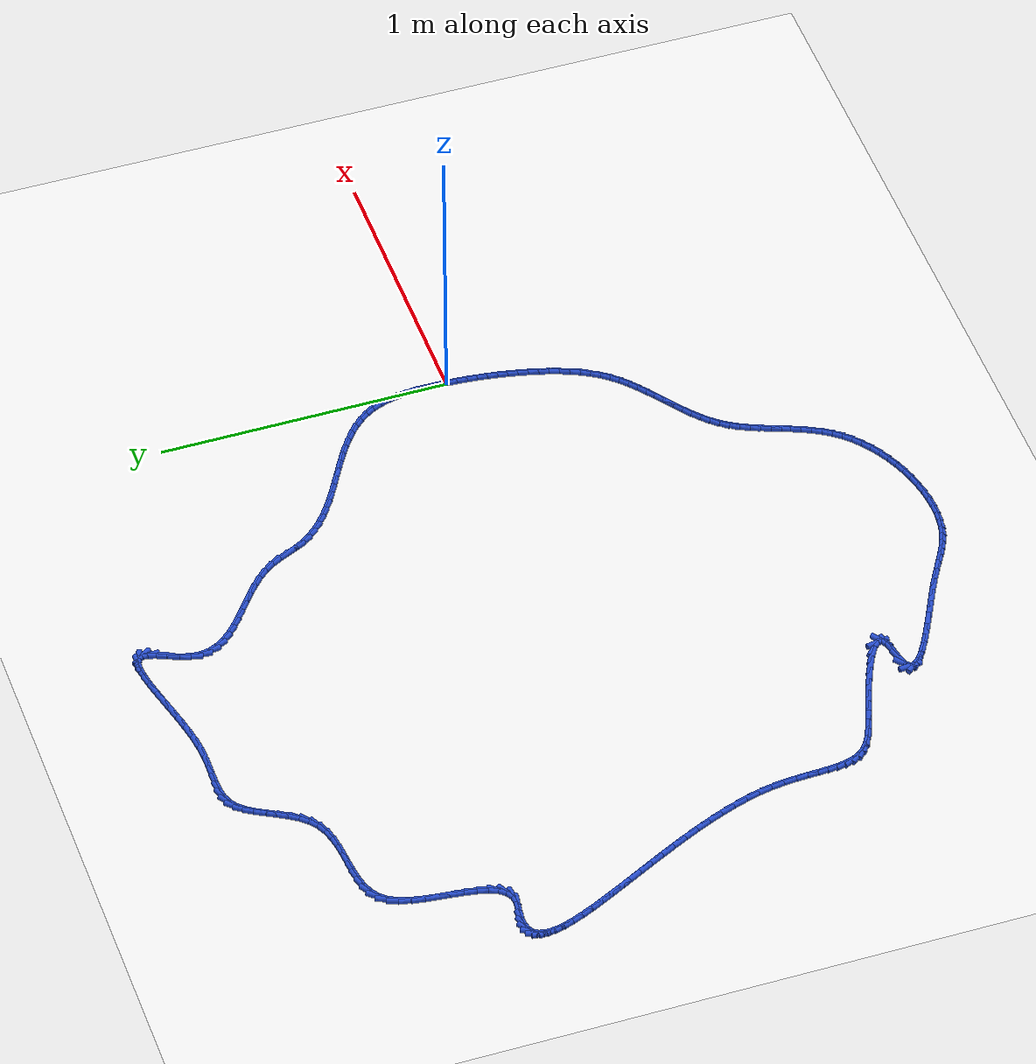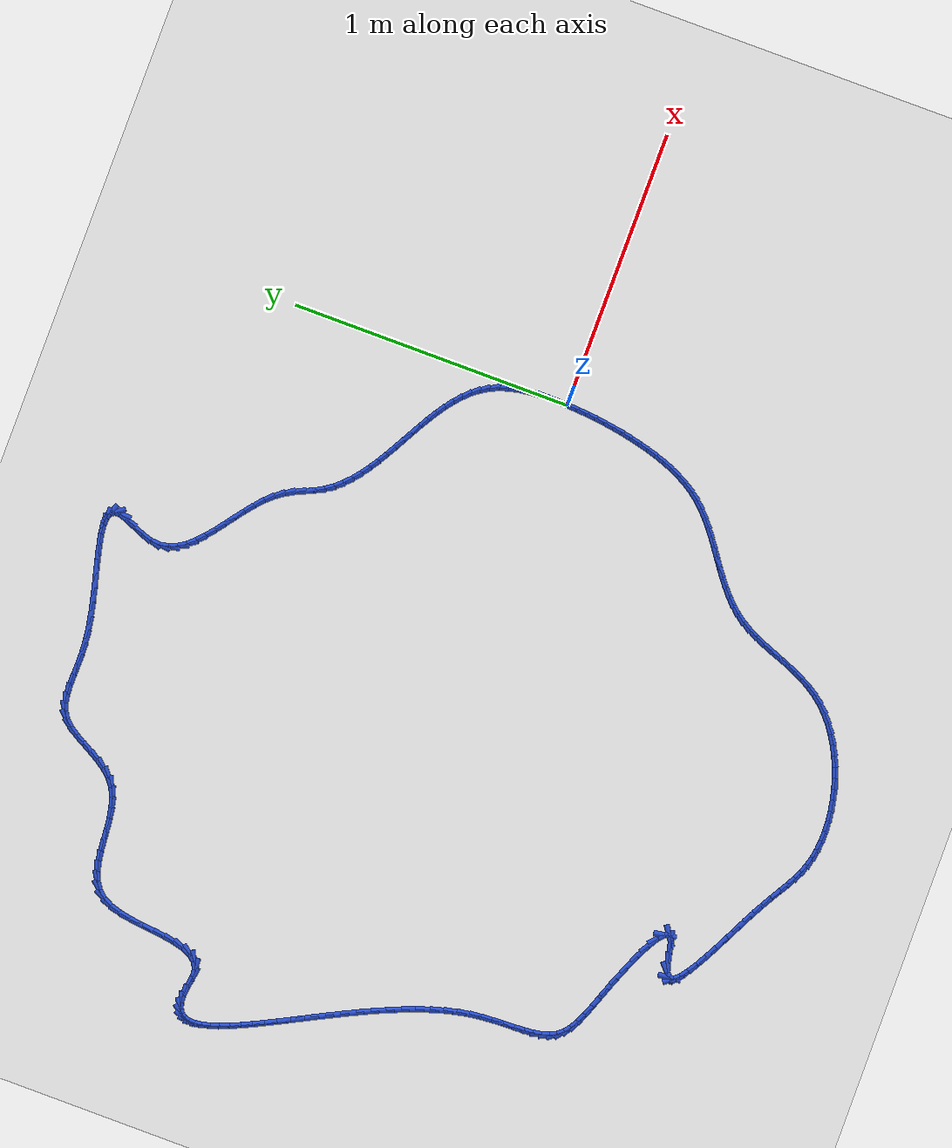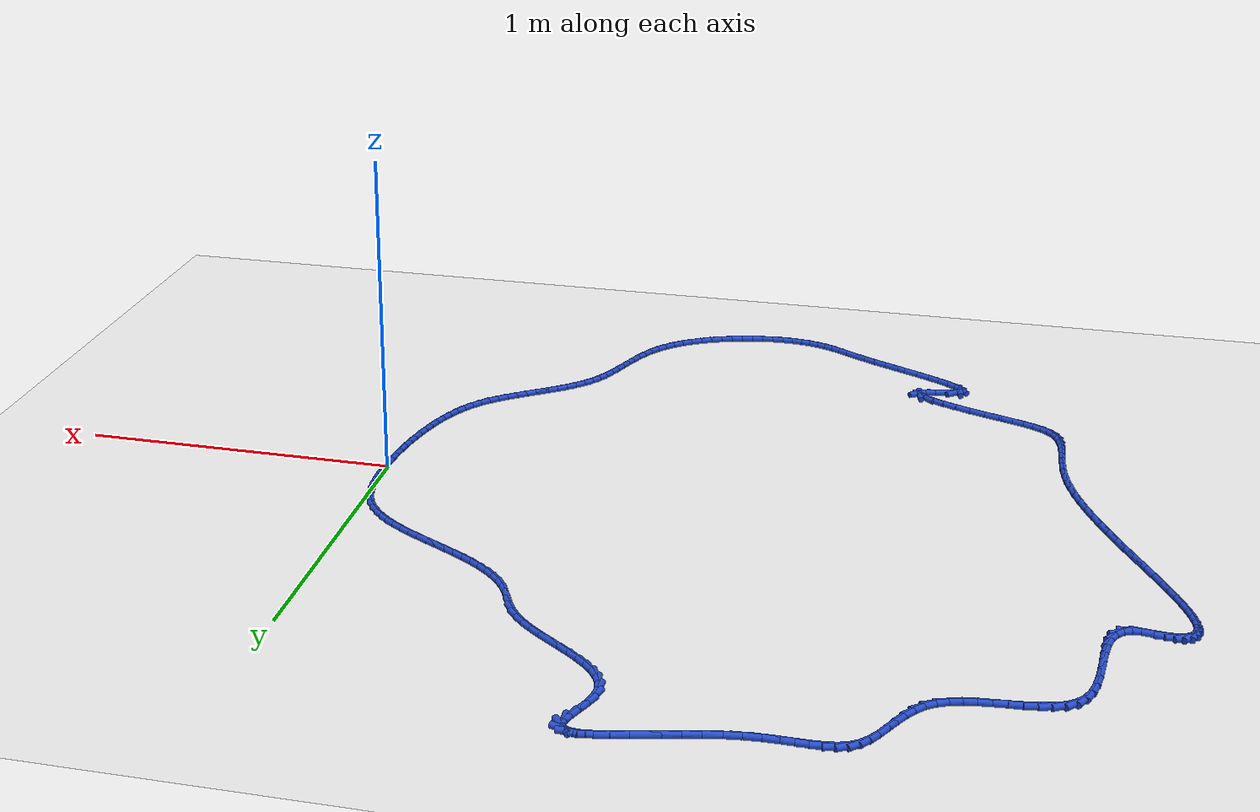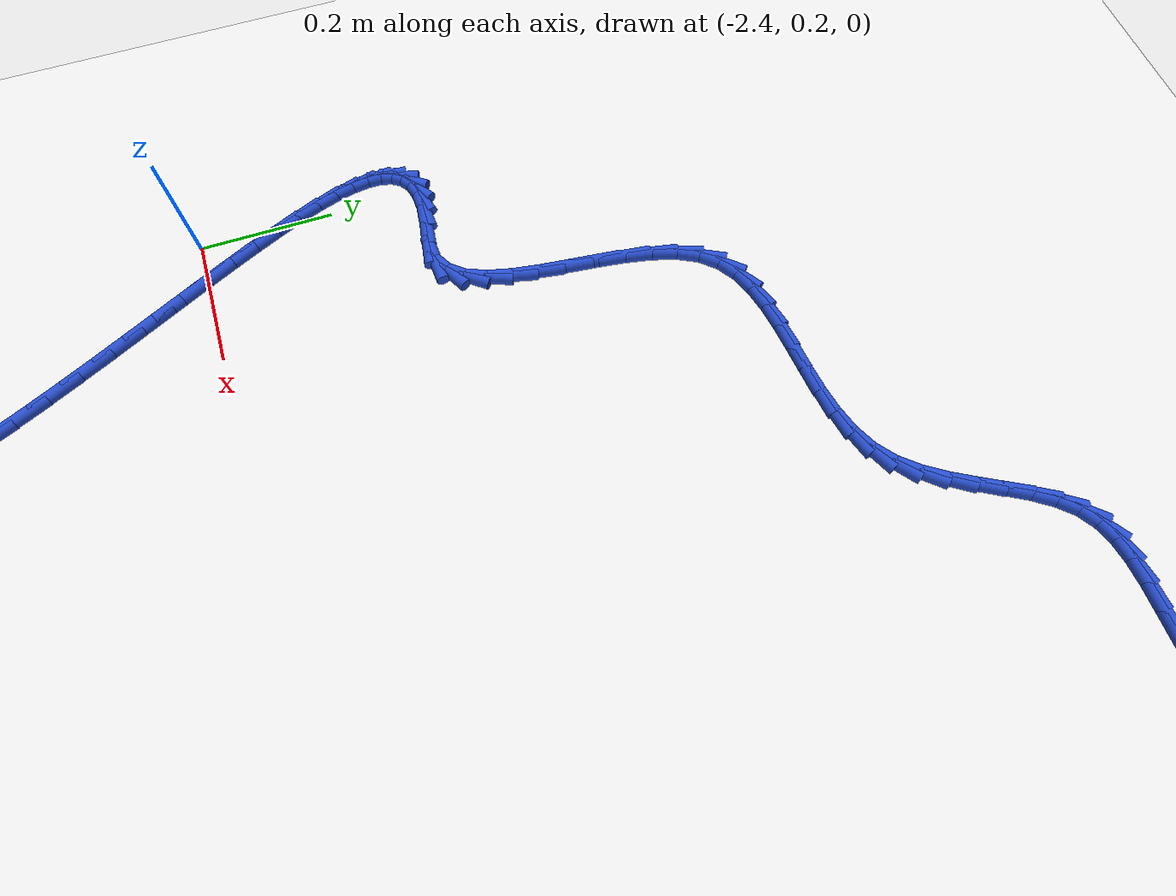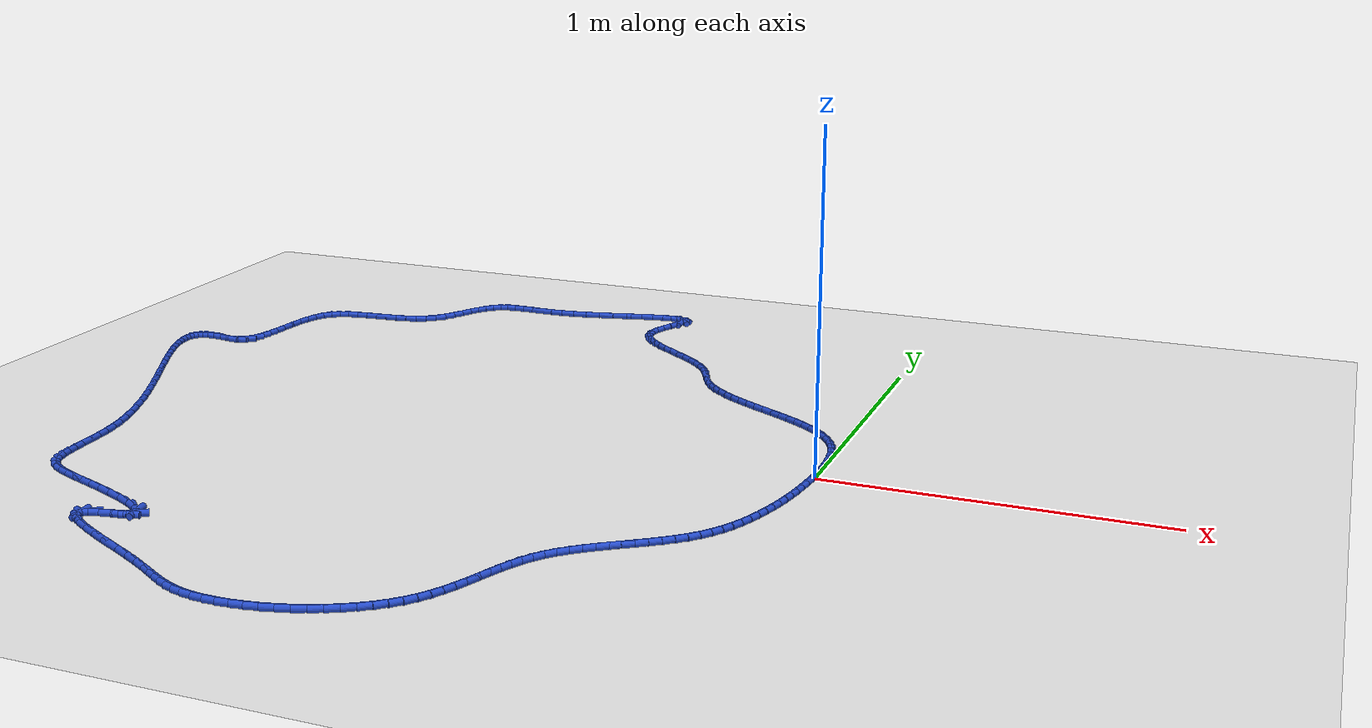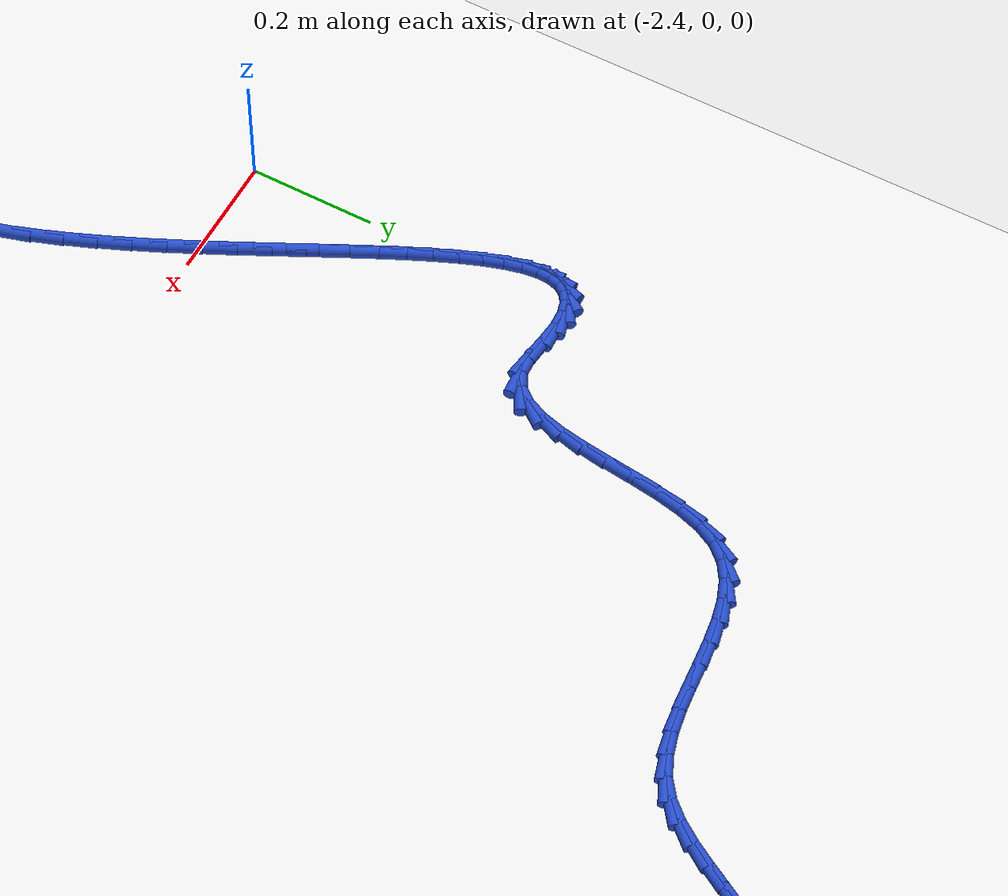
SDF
<sdf version="1.6">
 <world name="default">
  <light name="sun" type="directional">
   <pose>0 0 10 0 -0 0</pose>
   <diffuse>0.8 0.8 0.8 1</diffuse>
   <specular>0.2 0.2 0.2 1</specular>
   <attenuation>
    <range>1000</range>
    <constant>0.9</constant>
    <linear>0.01</linear>
    <quadratic>0.001</quadratic>
   </attenuation>
   <direction>-0.5 0.1 -0.9</direction>
  </light>
  <model name="ground_plane">
   <static>1</static>
   <link name="link">
    <collision name="collision">
     <geometry><plane><normal>0 0 1</normal><size>100 100</size></plane></geometry>
     <surface><friction><ode><mu>100</mu><mu2>50</mu2></ode></friction></surface>
    </collision>
    <visual name="visual">
     <cast_shadows>0</cast_shadows>
     <geometry><plane><normal>0 0 1</normal><size>100 100</size></plane></geometry>
     <material>
      <script><uri>file://media/materials/scripts/gazebo.material</uri><name>Gazebo/WhiteGlow</name></script>
     </material>
    </visual>
   </link>
  </model>
  <gravity>0 0 -9.8</gravity>
  <magnetic_field>6e-06 2.3e-05 -4.2e-05</magnetic_field>
  <atmosphere type="adiabatic"/>
  <physics name="default_physics" default="0" type="ode">
   <max_step_size>0.001</max_step_size>
   <real_time_factor>1</real_time_factor>
   <real_time_update_rate>1000</real_time_update_rate>
  </physics>
  <scene><ambient>0.4 0.4 0.4 1</ambient><background>0.7 0.7 0.7 1</background><shadows>1</shadows></scene>
  <spherical_coordinates>
   <surface_model>EARTH_WGS84</surface_model>
   <latitude_deg>0</latitude_deg>
   <longitude_deg>0</longitude_deg>
   <elevation>0</elevation>
   <heading_deg>0</heading_deg>
  </spherical_coordinates>
  <model name="line">
   <link name="link_0">
    <pose>-2.4936649967166602e-18 5.551115123125783e-17 0.01 0 1.57 1.535264560343441</pose>
    <collision name="collision">
     <geometry><cylinder><radius>0.01</radius><length>0.08</length></cylinder></geometry>
    </collision>
    <visual name="visual">
     <material>
      <script><name>Gazebo/Blue</name><uri>file://media/materials/scripts/gazebo.material</uri></script>
     </material>
     <geometry><cylinder><radius>0.01</radius><length>0.08</length></cylinder></geometry>
    </visual>
   </link>
   <link name="link_1">
    <pose>0.0012840881396828975 0.03612394858287934 0.01 0 1.57 1.5645498038746073</pose>
    <collision name="collision">
     <geometry><cylinder><radius>0.01</radius><length>0.08</length></cylinder></geometry>
    </collision>
    <visual name="visual">
     <material>
      <script><name>Gazebo/Blue</name><uri>file://media/materials/scripts/gazebo.material</uri></script>
     </material>
     <geometry><cylinder><radius>0.01</radius><length>0.08</length></cylinder></geometry>
    </visual>
   </link>
   <link name="link_2">
    <pose>0.001511256495549066 0.07249064476349956 0.01 0 1.57 -1.537835676432726</pose>
    <collision name="collision">
     <geometry><cylinder><radius>0.01</radius><length>0.08</length></cylinder></geometry>
    </collision>
    <visual name="visual">
     <material>
      <script><name>Gazebo/Blue</name><uri>file://media/materials/scripts/gazebo.material</uri></script>
     </material>
     <geometry><cylinder><radius>0.01</radius><length>0.08</length></cylinder></geometry>
    </visual>
   </link>
   <link name="link_3">
    <pose>0.00031643169811582843 0.1087275534804072 0.01 0 1.57 -1.4875436775994095</pose>
    <collision name="collision">
     <geometry><cylinder><radius>0.01</radius><length>0.08</length></cylinder></geometry>
    </collision>
    <visual name="visual">
     <material>
      <script><name>Gazebo/Blue</name><uri>file://media/materials/scripts/gazebo.material</uri></script>
     </material>
     <geometry><cylinder><radius>0.01</radius><length>0.08</length></cylinder></geometry>
    </visual>
   </link>
   <link name="link_4">
    <pose>-0.0026654596220994893 0.14446213967214855 0.01 0 1.57 -1.4245706592259852</pose>
    <collision name="collision">
     <geometry><cylinder><radius>0.01</radius><length>0.08</length></cylinder></geometry>
    </collision>
    <visual name="visual">
     <material>
      <script><name>Gazebo/Blue</name><uri>file://media/materials/scripts/gazebo.material</uri></script>
     </material>
     <geometry><cylinder><radius>0.01</radius><length>0.08</length></cylinder></geometry>
    </visual>
   </link>
   <link name="link_5">
    <pose>-0.007799490834579564 0.17932186827727012 0.01 0 1.57 -1.3469780910860145</pose>
    <collision name="collision">
     <geometry><cylinder><radius>0.01</radius><length>0.08</length></cylinder></geometry>
    </collision>
    <visual name="visual">
     <material>
      <script><name>Gazebo/Blue</name><uri>file://media/materials/scripts/gazebo.material</uri></script>
     </material>
     <geometry><cylinder><radius>0.01</radius><length>0.08</length></cylinder></geometry>
    </visual>
   </link>
   <link name="link_6">
    <pose>-0.015450735308807074 0.21293420423431814 0.01 0 1.57 -1.2527243977224605</pose>
    <collision name="collision">
     <geometry><cylinder><radius>0.01</radius><length>0.08</length></cylinder></geometry>
    </collision>
    <visual name="visual">
     <material>
      <script><name>Gazebo/Blue</name><uri>file://media/materials/scripts/gazebo.material</uri></script>
     </material>
     <geometry><cylinder><radius>0.01</radius><length>0.08</length></cylinder></geometry>
    </visual>
   </link>
   <link name="link_7">
    <pose>-0.02598426641426469 0.2449266124818391 0.01 0 1.57 -1.1402078588252762</pose>
    <collision name="collision">
     <geometry><cylinder><radius>0.01</radius><length>0.08</length></cylinder></geometry>
    </collision>
    <visual name="visual">
     <material>
      <script><name>Gazebo/Blue</name><uri>file://media/materials/scripts/gazebo.material</uri></script>
     </material>
     <geometry><cylinder><radius>0.01</radius><length>0.08</length></cylinder></geometry>
    </visual>
   </link>
   <link name="link_8">
    <pose>-0.03976450074796819 0.2749271144876108 0.01 0 1.57 -1.0167529269258861</pose>
    <collision name="collision">
     <geometry><cylinder><radius>0.01</radius><length>0.08</length></cylinder></geometry>
    </collision>
    <visual name="visual">
     <material>
      <script><name>Gazebo/Blue</name><uri>file://media/materials/scripts/gazebo.material</uri></script>
     </material>
     <geometry><cylinder><radius>0.01</radius><length>0.08</length></cylinder></geometry>
    </visual>
   </link>
   <link name="link_9">
    <pose>-0.05696358617402109 0.30272665445989344 0.01 0 1.57 -0.902973784058819</pose>
    <collision name="collision">
     <geometry><cylinder><radius>0.01</radius><length>0.08</length></cylinder></geometry>
    </collision>
    <visual name="visual">
     <material>
      <script><name>Gazebo/Blue</name><uri>file://media/materials/scripts/gazebo.material</uri></script>
     </material>
     <geometry><cylinder><radius>0.01</radius><length>0.08</length></cylinder></geometry>
    </visual>
   </link>
   <link name="link_10">
    <pose>-0.07729515361204115 0.3285047100726929 0.01 0 1.57 -0.8041195126919239</pose>
    <collision name="collision">
     <geometry><cylinder><radius>0.01</radius><length>0.08</length></cylinder></geometry>
    </collision>
    <visual name="visual">
     <material>
      <script><name>Gazebo/Blue</name><uri>file://media/materials/scripts/gazebo.material</uri></script>
     </material>
     <geometry><cylinder><radius>0.01</radius><length>0.08</length></cylinder></geometry>
    </visual>
   </link>
   <link name="link_11">
    <pose>-0.10040594108653329 0.35249744202707567 0.01 0 1.57 -0.7210196351180401</pose>
    <collision name="collision">
     <geometry><cylinder><radius>0.01</radius><length>0.08</length></cylinder></geometry>
    </collision>
    <visual name="visual">
     <material>
      <script><name>Gazebo/Blue</name><uri>file://media/materials/scripts/gazebo.material</uri></script>
     </material>
     <geometry><cylinder><radius>0.01</radius><length>0.08</length></cylinder></geometry>
    </visual>
   </link>
   <link name="link_12">
    <pose>-0.12594268662200245 0.37494101102410843 0.01 0 1.57 -0.6532456504707997</pose>
    <collision name="collision">
     <geometry><cylinder><radius>0.01</radius><length>0.08</length></cylinder></geometry>
    </collision>
    <visual name="visual">
     <material>
      <script><name>Gazebo/Blue</name><uri>file://media/materials/scripts/gazebo.material</uri></script>
     </material>
     <geometry><cylinder><radius>0.01</radius><length>0.08</length></cylinder></geometry>
    </visual>
   </link>
   <link name="link_13">
    <pose>-0.15355212824295347 0.3960715777648578 0.01 0 1.57 -0.5997389390181905</pose>
    <collision name="collision">
     <geometry><cylinder><radius>0.01</radius><length>0.08</length></cylinder></geometry>
    </collision>
    <visual name="visual">
     <material>
      <script><name>Gazebo/Blue</name><uri>file://media/materials/scripts/gazebo.material</uri></script>
     </material>
     <geometry><cylinder><radius>0.01</radius><length>0.08</length></cylinder></geometry>
    </visual>
   </link>
   <link name="link_14">
    <pose>-0.18288100397389134 0.4161253029503904 0.01 0 1.57 -0.5592699772801594</pose>
    <collision name="collision">
     <geometry><cylinder><radius>0.01</radius><length>0.08</length></cylinder></geometry>
    </collision>
    <visual name="visual">
     <material>
      <script><name>Gazebo/Blue</name><uri>file://media/materials/scripts/gazebo.material</uri></script>
     </material>
     <geometry><cylinder><radius>0.01</radius><length>0.08</length></cylinder></geometry>
    </visual>
   </link>
   <link name="link_15">
    <pose>-0.21357605183932088 0.4353383472817726 0.01 0 1.57 -0.5307108991946913</pose>
    <collision name="collision">
     <geometry><cylinder><radius>0.01</radius><length>0.08</length></cylinder></geometry>
    </collision>
    <visual name="visual">
     <material>
      <script><name>Gazebo/Blue</name><uri>file://media/materials/scripts/gazebo.material</uri></script>
     </material>
     <geometry><cylinder><radius>0.01</radius><length>0.08</length></cylinder></geometry>
    </visual>
   </link>
   <link name="link_16">
    <pose>-0.2452840098637471 0.45394687146007123 0.01 0 1.57 -0.513172665324931</pose>
    <collision name="collision">
     <geometry><cylinder><radius>0.01</radius><length>0.08</length></cylinder></geometry>
    </collision>
    <visual name="visual">
     <material>
      <script><name>Gazebo/Blue</name><uri>file://media/materials/scripts/gazebo.material</uri></script>
     </material>
     <geometry><cylinder><radius>0.01</radius><length>0.08</length></cylinder></geometry>
    </visual>
   </link>
   <link name="link_17">
    <pose>-0.2776516160716749 0.4721870361863528 0.01 0 1.57 -0.5060629812694932</pose>
    <collision name="collision">
     <geometry><cylinder><radius>0.01</radius><length>0.08</length></cylinder></geometry>
    </collision>
    <visual name="visual">
     <material>
      <script><name>Gazebo/Blue</name><uri>file://media/materials/scripts/gazebo.material</uri></script>
     </material>
     <geometry><cylinder><radius>0.01</radius><length>0.08</length></cylinder></geometry>
    </visual>
   </link>
   <link name="link_18">
    <pose>-0.31032560848760915 0.49029500216168387 0.01 0 1.57 -0.5091046381326408</pose>
    <collision name="collision">
     <geometry><cylinder><radius>0.01</radius><length>0.08</length></cylinder></geometry>
    </collision>
    <visual name="visual">
     <material>
      <script><name>Gazebo/Blue</name><uri>file://media/materials/scripts/gazebo.material</uri></script>
     </material>
     <geometry><cylinder><radius>0.01</radius><length>0.08</length></cylinder></geometry>
    </visual>
   </link>
   <link name="link_19">
    <pose>-0.3429527251360547 0.5085069300871311 0.01 0 1.57 -0.522336389650863</pose>
    <collision name="collision">
     <geometry><cylinder><radius>0.01</radius><length>0.08</length></cylinder></geometry>
    </collision>
    <visual name="visual">
     <material>
      <script><name>Gazebo/Blue</name><uri>file://media/materials/scripts/gazebo.material</uri></script>
     </material>
     <geometry><cylinder><radius>0.01</radius><length>0.08</length></cylinder></geometry>
    </visual>
   </link>
   <link name="link_20">
    <pose>-0.37517970404151657 0.5270589806637608 0.01 0 1.57 -0.5461047270690569</pose>
    <collision name="collision">
     <geometry><cylinder><radius>0.01</radius><length>0.08</length></cylinder></geometry>
    </collision>
    <visual name="visual">
     <material>
      <script><name>Gazebo/Blue</name><uri>file://media/materials/scripts/gazebo.material</uri></script>
     </material>
     <geometry><cylinder><radius>0.01</radius><length>0.08</length></cylinder></geometry>
    </visual>
   </link>
   <link name="link_21">
    <pose>-0.4066532832284995 0.5461873145926399 0.01 0 1.57 -0.5810437528685014</pose>
    <collision name="collision">
     <geometry><cylinder><radius>0.01</radius><length>0.08</length></cylinder></geometry>
    </collision>
    <visual name="visual">
     <material>
      <script><name>Gazebo/Blue</name><uri>file://media/materials/scripts/gazebo.material</uri></script>
     </material>
     <geometry><cylinder><radius>0.01</radius><length>0.08</length></cylinder></geometry>
    </visual>
   </link>
   <link name="link_22">
    <pose>-0.43702020072150877 0.5661280925748349 0.01 0 1.57 -0.6280291603514226</pose>
    <collision name="collision">
     <geometry><cylinder><radius>0.01</radius><length>0.08</length></cylinder></geometry>
    </collision>
    <visual name="visual">
     <material>
      <script><name>Gazebo/Blue</name><uri>file://media/materials/scripts/gazebo.material</uri></script>
     </material>
     <geometry><cylinder><radius>0.01</radius><length>0.08</length></cylinder></geometry>
    </visual>
   </link>
   <link name="link_23">
    <pose>-0.4659271945450489 0.5871174753114121 0.01 0 1.57 -0.6880792725380012</pose>
    <collision name="collision">
     <geometry><cylinder><radius>0.01</radius><length>0.08</length></cylinder></geometry>
    </collision>
    <visual name="visual">
     <material>
      <script><name>Gazebo/Blue</name><uri>file://media/materials/scripts/gazebo.material</uri></script>
     </material>
     <geometry><cylinder><radius>0.01</radius><length>0.08</length></cylinder></geometry>
    </visual>
   </link>
   <link name="link_24">
    <pose>-0.49302100272362503 0.6093916235034388 0.01 0 1.57 -0.7621628214494885</pose>
    <collision name="collision">
     <geometry><cylinder><radius>0.01</radius><length>0.08</length></cylinder></geometry>
    </collision>
    <visual name="visual">
     <material>
      <script><name>Gazebo/Blue</name><uri>file://media/materials/scripts/gazebo.material</uri></script>
     </material>
     <geometry><cylinder><radius>0.01</radius><length>0.08</length></cylinder></geometry>
    </visual>
   </link>
   <link name="link_25">
    <pose>-0.517948363281742 0.6331866978519807 0.01 0 1.57 -0.8508699777177273</pose>
    <collision name="collision">
     <geometry><cylinder><radius>0.01</radius><length>0.08</length></cylinder></geometry>
    </collision>
    <visual name="visual">
     <material>
      <script><name>Gazebo/Blue</name><uri>file://media/materials/scripts/gazebo.material</uri></script>
     </material>
     <geometry><cylinder><radius>0.01</radius><length>0.08</length></cylinder></geometry>
    </visual>
   </link>
   <link name="link_26">
    <pose>-0.5403560142439046 0.6587388590581049 0.01 0 1.57 -0.9539351848461627</pose>
    <collision name="collision">
     <geometry><cylinder><radius>0.01</radius><length>0.08</length></cylinder></geometry>
    </collision>
    <visual name="visual">
     <material>
      <script><name>Gazebo/Blue</name><uri>file://media/materials/scripts/gazebo.material</uri></script>
     </material>
     <geometry><cylinder><radius>0.01</radius><length>0.08</length></cylinder></geometry>
    </visual>
   </link>
   <link name="link_27">
    <pose>-0.559890693634618 0.686284267822878 0.01 0 1.57 -1.0650247604263254</pose>
    <collision name="collision">
     <geometry><cylinder><radius>0.01</radius><length>0.08</length></cylinder></geometry>
    </collision>
    <visual name="visual">
     <material>
      <script><name>Gazebo/Blue</name><uri>file://media/materials/scripts/gazebo.material</uri></script>
     </material>
     <geometry><cylinder><radius>0.01</radius><length>0.08</length></cylinder></geometry>
    </visual>
   </link>
   <link name="link_28">
    <pose>-0.5763384373440941 0.7159829666899207 0.01 0 1.57 -1.1340277420790987</pose>
    <collision name="collision">
     <geometry><cylinder><radius>0.01</radius><length>0.08</length></cylinder></geometry>
    </collision>
    <visual name="visual">
     <material>
      <script><name>Gazebo/Blue</name><uri>file://media/materials/scripts/gazebo.material</uri></script>
     </material>
     <geometry><cylinder><radius>0.01</radius><length>0.08</length></cylinder></geometry>
    </visual>
   </link>
   <link name="link_29">
    <pose>-0.5909175316045487 0.747212356943557 0.01 0 1.57 -1.1344712018497798</pose>
    <collision name="collision">
     <geometry><cylinder><radius>0.01</radius><length>0.08</length></cylinder></geometry>
    </collision>
    <visual name="visual">
     <material>
      <script><name>Gazebo/Blue</name><uri>file://media/materials/scripts/gazebo.material</uri></script>
     </material>
     <geometry><cylinder><radius>0.01</radius><length>0.08</length></cylinder></geometry>
    </visual>
   </link>
   <link name="link_30">
    <pose>-0.6056885783829699 0.7788895634568915 0.01 0 1.57 -1.0688330388672136</pose>
    <collision name="collision">
     <geometry><cylinder><radius>0.01</radius><length>0.08</length></cylinder></geometry>
    </collision>
    <visual name="visual">
     <material>
      <script><name>Gazebo/Blue</name><uri>file://media/materials/scripts/gazebo.material</uri></script>
     </material>
     <geometry><cylinder><radius>0.01</radius><length>0.08</length></cylinder></geometry>
    </visual>
   </link>
   <link name="link_31">
    <pose>-0.6227229647555037 0.8099258176700388 0.01 0 1.57 -0.9468083116000312</pose>
    <collision name="collision">
     <geometry><cylinder><radius>0.01</radius><length>0.08</length></cylinder></geometry>
    </collision>
    <visual name="visual">
     <material>
      <script><name>Gazebo/Blue</name><uri>file://media/materials/scripts/gazebo.material</uri></script>
     </material>
     <geometry><cylinder><radius>0.01</radius><length>0.08</length></cylinder></geometry>
    </visual>
   </link>
   <link name="link_32">
    <pose>-0.6438899885591162 0.8393266342364513 0.01 0 1.57 -0.8292757306958182</pose>
    <collision name="collision">
     <geometry><cylinder><radius>0.01</radius><length>0.08</length></cylinder></geometry>
    </collision>
    <visual name="visual">
     <material>
      <script><name>Gazebo/Blue</name><uri>file://media/materials/scripts/gazebo.material</uri></script>
     </material>
     <geometry><cylinder><radius>0.01</radius><length>0.08</length></cylinder></geometry>
    </visual>
   </link>
   <link name="link_33">
    <pose>-0.6692023024793812 0.8669637316292895 0.01 0 1.57 -0.7440916666252301</pose>
    <collision name="collision">
     <geometry><cylinder><radius>0.01</radius><length>0.08</length></cylinder></geometry>
    </collision>
    <visual name="visual">
     <material>
      <script><name>Gazebo/Blue</name><uri>file://media/materials/scripts/gazebo.material</uri></script>
     </material>
     <geometry><cylinder><radius>0.01</radius><length>0.08</length></cylinder></geometry>
    </visual>
   </link>
   <link name="link_34">
    <pose>-0.6976735183635517 0.893174923304674 0.01 0 1.57 -0.6869666223439104</pose>
    <collision name="collision">
     <geometry><cylinder><radius>0.01</radius><length>0.08</length></cylinder></geometry>
    </collision>
    <visual name="visual">
     <material>
      <script><name>Gazebo/Blue</name><uri>file://media/materials/scripts/gazebo.material</uri></script>
     </material>
     <geometry><cylinder><radius>0.01</radius><length>0.08</length></cylinder></geometry>
    </visual>
   </link>
   <link name="link_35">
    <pose>-0.7283076159622943 0.9183025165008822 0.01 0 1.57 -0.6541929618392293</pose>
    <collision name="collision">
     <geometry><cylinder><radius>0.01</radius><length>0.08</length></cylinder></geometry>
    </collision>
    <visual name="visual">
     <material>
      <script><name>Gazebo/Blue</name><uri>file://media/materials/scripts/gazebo.material</uri></script>
     </material>
     <geometry><cylinder><radius>0.01</radius><length>0.08</length></cylinder></geometry>
    </visual>
   </link>
   <link name="link_36">
    <pose>-0.7601085750262758 0.9426888184561922 0.01 0 1.57 -0.6436705914752291</pose>
    <collision name="collision">
     <geometry><cylinder><radius>0.01</radius><length>0.08</length></cylinder></geometry>
    </collision>
    <visual name="visual">
     <material>
      <script><name>Gazebo/Blue</name><uri>file://media/materials/scripts/gazebo.material</uri></script>
     </material>
     <geometry><cylinder><radius>0.01</radius><length>0.08</length></cylinder></geometry>
    </visual>
   </link>
   <link name="link_37">
    <pose>-0.7920803753061628 0.9666761364088811 0.01 0 1.57 -0.6551245771189139</pose>
    <collision name="collision">
     <geometry><cylinder><radius>0.01</radius><length>0.08</length></cylinder></geometry>
    </collision>
    <visual name="visual">
     <material>
      <script><name>Gazebo/Blue</name><uri>file://media/materials/scripts/gazebo.material</uri></script>
     </material>
     <geometry><cylinder><radius>0.01</radius><length>0.08</length></cylinder></geometry>
    </visual>
   </link>
   <link name="link_38">
    <pose>-0.823226996552622 0.9906067775972272 0.01 0 1.57 -0.6902624537019658</pose>
    <collision name="collision">
     <geometry><cylinder><radius>0.01</radius><length>0.08</length></cylinder></geometry>
    </collision>
    <visual name="visual">
     <material>
      <script><name>Gazebo/Blue</name><uri>file://media/materials/scripts/gazebo.material</uri></script>
     </material>
     <geometry><cylinder><radius>0.01</radius><length>0.08</length></cylinder></geometry>
    </visual>
   </link>
   <link name="link_39">
    <pose>-0.8525524185163205 1.0148230492595076 0.01 0 1.57 -0.7530060910809215</pose>
    <collision name="collision">
     <geometry><cylinder><radius>0.01</radius><length>0.08</length></cylinder></geometry>
    </collision>
    <visual name="visual">
     <material>
      <script><name>Gazebo/Blue</name><uri>file://media/materials/scripts/gazebo.material</uri></script>
     </material>
     <geometry><cylinder><radius>0.01</radius><length>0.08</length></cylinder></geometry>
    </visual>
   </link>
   <link name="link_40">
    <pose>-0.8790606209479246 1.0396672586340006 0.01 0 1.57 -0.8496166679970097</pose>
    <collision name="collision">
     <geometry><cylinder><radius>0.01</radius><length>0.08</length></cylinder></geometry>
    </collision>
    <visual name="visual">
     <material>
      <script><name>Gazebo/Blue</name><uri>file://media/materials/scripts/gazebo.material</uri></script>
     </material>
     <geometry><cylinder><radius>0.01</radius><length>0.08</length></cylinder></geometry>
    </visual>
   </link>
   <link name="link_41">
    <pose>-0.9017555835981016 1.0654817129589833 0.01 0 1.57 -0.9878887949472469</pose>
    <collision name="collision">
     <geometry><cylinder><radius>0.01</radius><length>0.08</length></cylinder></geometry>
    </collision>
    <visual name="visual">
     <material>
      <script><name>Gazebo/Blue</name><uri>file://media/materials/scripts/gazebo.material</uri></script>
     </material>
     <geometry><cylinder><radius>0.01</radius><length>0.08</length></cylinder></geometry>
    </visual>
   </link>
   <link name="link_42">
    <pose>-0.9196412862175176 1.092608719472734 0.01 0 1.57 -1.1734034912138087</pose>
    <collision name="collision">
     <geometry><cylinder><radius>0.01</radius><length>0.08</length></cylinder></geometry>
    </collision>
    <visual name="visual">
     <material>
      <script><name>Gazebo/Blue</name><uri>file://media/materials/scripts/gazebo.material</uri></script>
     </material>
     <geometry><cylinder><radius>0.01</radius><length>0.08</length></cylinder></geometry>
    </visual>
   </link>
   <link name="link_43">
    <pose>-0.9317217085568399 1.12139058541353 0.01 0 1.57 -1.400932324442134</pose>
    <collision name="collision">
     <geometry><cylinder><radius>0.01</radius><length>0.08</length></cylinder></geometry>
    </collision>
    <visual name="visual">
     <material>
      <script><name>Gazebo/Blue</name><uri>file://media/materials/scripts/gazebo.material</uri></script>
     </material>
     <geometry><cylinder><radius>0.01</radius><length>0.08</length></cylinder></geometry>
    </visual>
   </link>
   <link name="link_44">
    <pose>-0.9370008303667352 1.1521696180196497 0.01 0 1.57 1.4949063477040772</pose>
    <collision name="collision">
     <geometry><cylinder><radius>0.01</radius><length>0.08</length></cylinder></geometry>
    </collision>
    <visual name="visual">
     <material>
      <script><name>Gazebo/Blue</name><uri>file://media/materials/scripts/gazebo.material</uri></script>
     </material>
     <geometry><cylinder><radius>0.01</radius><length>0.08</length></cylinder></geometry>
    </visual>
   </link>
   <link name="link_45">
    <pose>-0.93448263139787 1.1852881245293698 0.01 0 1.57 1.2835616166285895</pose>
    <collision name="collision">
     <geometry><cylinder><radius>0.01</radius><length>0.08</length></cylinder></geometry>
    </collision>
    <visual name="visual">
     <material>
      <script><name>Gazebo/Blue</name><uri>file://media/materials/scripts/gazebo.material</uri></script>
     </material>
     <geometry><cylinder><radius>0.01</radius><length>0.08</length></cylinder></geometry>
    </visual>
   </link>
   <link name="link_46">
    <pose>-0.9240426888932335 1.2206293938082275 0.01 0 1.57 1.1787719265545076</pose>
    <collision name="collision">
     <geometry><cylinder><radius>0.01</radius><length>0.08</length></cylinder></geometry>
    </collision>
    <visual name="visual">
     <material>
      <script><name>Gazebo/Blue</name><uri>file://media/materials/scripts/gazebo.material</uri></script>
     </material>
     <geometry><cylinder><radius>0.01</radius><length>0.08</length></cylinder></geometry>
    </visual>
   </link>
   <link name="link_47">
    <pose>-0.9093973185417629 1.2560540270395273 0.01 0 1.57 1.165524495738626</pose>
    <collision name="collision">
     <geometry><cylinder><radius>0.01</radius><length>0.08</length></cylinder></geometry>
    </collision>
    <visual name="visual">
     <material>
      <script><name>Gazebo/Blue</name><uri>file://media/materials/scripts/gazebo.material</uri></script>
     </material>
     <geometry><cylinder><radius>0.01</radius><length>0.08</length></cylinder></geometry>
    </visual>
   </link>
   <link name="link_48">
    <pose>-0.895320430142908 1.2888656537173426 0.01 0 1.57 1.263280046463911</pose>
    <collision name="collision">
     <geometry><cylinder><radius>0.01</radius><length>0.08</length></cylinder></geometry>
    </collision>
    <visual name="visual">
     <material>
      <script><name>Gazebo/Blue</name><uri>file://media/materials/scripts/gazebo.material</uri></script>
     </material>
     <geometry><cylinder><radius>0.01</radius><length>0.08</length></cylinder></geometry>
    </visual>
   </link>
   <link name="link_49">
    <pose>-0.8865859657416556 1.3163678863539487 0.01 0 1.57 -1.545657544549913</pose>
    <collision name="collision">
     <geometry><cylinder><radius>0.01</radius><length>0.08</length></cylinder></geometry>
    </collision>
    <visual name="visual">
     <material>
      <script><name>Gazebo/Blue</name><uri>file://media/materials/scripts/gazebo.material</uri></script>
     </material>
     <geometry><cylinder><radius>0.01</radius><length>0.08</length></cylinder></geometry>
    </visual>
   </link>
   <link name="link_50">
    <pose>-0.8870900028530839 1.3364138426464844 0.01 0 1.57 -0.9189617225608825</pose>
    <collision name="collision">
     <geometry><cylinder><radius>0.01</radius><length>0.08</length></cylinder></geometry>
    </collision>
    <visual name="visual">
     <material>
      <script><name>Gazebo/Blue</name><uri>file://media/materials/scripts/gazebo.material</uri></script>
     </material>
     <geometry><cylinder><radius>0.01</radius><length>0.08</length></cylinder></geometry>
    </visual>
   </link>
   <link name="link_51">
    <pose>-0.8968917106142243 1.3492583788015724 0.01 0 1.57 -0.3472248283309166</pose>
    <collision name="collision">
     <geometry><cylinder><radius>0.01</radius><length>0.08</length></cylinder></geometry>
    </collision>
    <visual name="visual">
     <material>
      <script><name>Gazebo/Blue</name><uri>file://media/materials/scripts/gazebo.material</uri></script>
     </material>
     <geometry><cylinder><radius>0.01</radius><length>0.08</length></cylinder></geometry>
    </visual>
   </link>
   <link name="link_52">
    <pose>-0.9150022665005942 1.3558123484287097 0.01 0 1.57 -0.04614286182634578</pose>
    <collision name="collision">
     <geometry><cylinder><radius>0.01</radius><length>0.08</length></cylinder></geometry>
    </collision>
    <visual name="visual">
     <material>
      <script><name>Gazebo/Blue</name><uri>file://media/materials/scripts/gazebo.material</uri></script>
     </material>
     <geometry><cylinder><radius>0.01</radius><length>0.08</length></cylinder></geometry>
    </visual>
   </link>
   <link name="link_53">
    <pose>-0.9404328232543714 1.356986620619394 0.01 0 1.57 0.10335766089260554</pose>
    <collision name="collision">
     <geometry><cylinder><radius>0.01</radius><length>0.08</length></cylinder></geometry>
    </collision>
    <visual name="visual">
     <material>
      <script><name>Gazebo/Blue</name><uri>file://media/materials/scripts/gazebo.material</uri></script>
     </material>
     <geometry><cylinder><radius>0.01</radius><length>0.08</length></cylinder></geometry>
    </visual>
   </link>
   <link name="link_54">
    <pose>-0.9721945336177331 1.3536920644651236 0.01 0 1.57 0.18262613280172227</pose>
    <collision name="collision">
     <geometry><cylinder><radius>0.01</radius><length>0.08</length></cylinder></geometry>
    </collision>
    <visual name="visual">
     <material>
      <script><name>Gazebo/Blue</name><uri>file://media/materials/scripts/gazebo.material</uri></script>
     </material>
     <geometry><cylinder><radius>0.01</radius><length>0.08</length></cylinder></geometry>
    </visual>
   </link>
   <link name="link_55">
    <pose>-1.009298550332857 1.3468395490573972 0.01 0 1.57 0.2252523496765217</pose>
    <collision name="collision">
     <geometry><cylinder><radius>0.01</radius><length>0.08</length></cylinder></geometry>
    </collision>
    <visual name="visual">
     <material>
      <script><name>Gazebo/Blue</name><uri>file://media/materials/scripts/gazebo.material</uri></script>
     </material>
     <geometry><cylinder><radius>0.01</radius><length>0.08</length></cylinder></geometry>
    </visual>
   </link>
   <link name="link_56">
    <pose>-1.0507560261419209 1.3373399434877125 0.01 0 1.57 0.24561490205891764</pose>
    <collision name="collision">
     <geometry><cylinder><radius>0.01</radius><length>0.08</length></cylinder></geometry>
    </collision>
    <visual name="visual">
     <material>
      <script><name>Gazebo/Blue</name><uri>file://media/materials/scripts/gazebo.material</uri></script>
     </material>
     <geometry><cylinder><radius>0.01</radius><length>0.08</length></cylinder></geometry>
    </visual>
   </link>
   <link name="link_57">
    <pose>-1.0955781137871012 1.326104116847567 0.01 0 1.57 0.2501907083706787</pose>
    <collision name="collision">
     <geometry><cylinder><radius>0.01</radius><length>0.08</length></cylinder></geometry>
    </collision>
    <visual name="visual">
     <material>
      <script><name>Gazebo/Blue</name><uri>file://media/materials/scripts/gazebo.material</uri></script>
     </material>
     <geometry><cylinder><radius>0.01</radius><length>0.08</length></cylinder></geometry>
    </visual>
   </link>
   <link name="link_58">
    <pose>-1.1427759660105758 1.3140429382284595 0.01 0 1.57 0.24167244742331714</pose>
    <collision name="collision">
     <geometry><cylinder><radius>0.01</radius><length>0.08</length></cylinder></geometry>
    </collision>
    <visual name="visual">
     <material>
      <script><name>Gazebo/Blue</name><uri>file://media/materials/scripts/gazebo.material</uri></script>
     </material>
     <geometry><cylinder><radius>0.01</radius><length>0.08</length></cylinder></geometry>
    </visual>
   </link>
   <link name="link_59">
    <pose>-1.1913607355545226 1.3020672767218873 0.01 0 1.57 0.22050081717408146</pose>
    <collision name="collision">
     <geometry><cylinder><radius>0.01</radius><length>0.08</length></cylinder></geometry>
    </collision>
    <visual name="visual">
     <material>
      <script><name>Gazebo/Blue</name><uri>file://media/materials/scripts/gazebo.material</uri></script>
     </material>
     <geometry><cylinder><radius>0.01</radius><length>0.08</length></cylinder></geometry>
    </visual>
   </link>
   <link name="link_60">
    <pose>-1.2403435751611183 1.291088001419349 0.01 0 1.57 0.18531817152036642</pose>
    <collision name="collision">
     <geometry><cylinder><radius>0.01</radius><length>0.08</length></cylinder></geometry>
    </collision>
    <visual name="visual">
     <material>
      <script><name>Gazebo/Blue</name><uri>file://media/materials/scripts/gazebo.material</uri></script>
     </material>
     <geometry><cylinder><radius>0.01</radius><length>0.08</length></cylinder></geometry>
    </visual>
   </link>
   <link name="link_61">
    <pose>-1.288735637572541 1.2820159814123426 0.01 0 1.57 0.1328083670905106</pose>
    <collision name="collision">
     <geometry><cylinder><radius>0.01</radius><length>0.08</length></cylinder></geometry>
    </collision>
    <visual name="visual">
     <material>
      <script><name>Gazebo/Blue</name><uri>file://media/materials/scripts/gazebo.material</uri></script>
     </material>
     <geometry><cylinder><radius>0.01</radius><length>0.08</length></cylinder></geometry>
    </visual>
   </link>
   <link name="link_62">
    <pose>-1.3355480755309672 1.2757620857923657 0.01 0 1.57 0.06440131818322936</pose>
    <collision name="collision">
     <geometry><cylinder><radius>0.01</radius><length>0.08</length></cylinder></geometry>
    </collision>
    <visual name="visual">
     <material>
      <script><name>Gazebo/Blue</name><uri>file://media/materials/scripts/gazebo.material</uri></script>
     </material>
     <geometry><cylinder><radius>0.01</radius><length>0.08</length></cylinder></geometry>
    </visual>
   </link>
   <link name="link_63">
    <pose>-1.379924092855706 1.2729002541758936 0.01 0 1.57 0.010593005569473775</pose>
    <collision name="collision">
     <geometry><cylinder><radius>0.01</radius><length>0.08</length></cylinder></geometry>
    </collision>
    <visual name="visual">
     <material>
      <script><name>Gazebo/Blue</name><uri>file://media/materials/scripts/gazebo.material</uri></script>
     </material>
     <geometry><cylinder><radius>0.01</radius><length>0.08</length></cylinder></geometry>
    </visual>
   </link>
   <link name="link_64">
    <pose>-1.4216127296190673 1.2724586296958642 0.01 0 1.57 -0.01448078470729559</pose>
    <collision name="collision">
     <geometry><cylinder><radius>0.01</radius><length>0.08</length></cylinder></geometry>
    </collision>
    <visual name="visual">
     <material>
      <script><name>Gazebo/Blue</name><uri>file://media/materials/scripts/gazebo.material</uri></script>
     </material>
     <geometry><cylinder><radius>0.01</radius><length>0.08</length></cylinder></geometry>
    </visual>
   </link>
   <link name="link_65">
    <pose>-1.4605366632716323 1.2730223182001337 0.01 0 1.57 -0.0042699918529151525</pose>
    <collision name="collision">
     <geometry><cylinder><radius>0.01</radius><length>0.08</length></cylinder></geometry>
    </collision>
    <visual name="visual">
     <material>
      <script><name>Gazebo/Blue</name><uri>file://media/materials/scripts/gazebo.material</uri></script>
     </material>
     <geometry><cylinder><radius>0.01</radius><length>0.08</length></cylinder></geometry>
    </visual>
   </link>
   <link name="link_66">
    <pose>-1.4966185857201906 1.2731763886514078 0.01 0 1.57 0.05032982186870994</pose>
    <collision name="collision">
     <geometry><cylinder><radius>0.01</radius><length>0.08</length></cylinder></geometry>
    </collision>
    <visual name="visual">
     <material>
      <script><name>Gazebo/Blue</name><uri>file://media/materials/scripts/gazebo.material</uri></script>
     </material>
     <geometry><cylinder><radius>0.01</radius><length>0.08</length></cylinder></geometry>
    </visual>
   </link>
   <link name="link_67">
    <pose>-1.5297811888715336 1.2715059100123953 0.01 0 1.57 0.1613498733237581</pose>
    <collision name="collision">
     <geometry><cylinder><radius>0.01</radius><length>0.08</length></cylinder></geometry>
    </collision>
    <visual name="visual">
     <material>
      <script><name>Gazebo/Blue</name><uri>file://media/materials/scripts/gazebo.material</uri></script>
     </material>
     <geometry><cylinder><radius>0.01</radius><length>0.08</length></cylinder></geometry>
    </visual>
   </link>
   <link name="link_68">
    <pose>-1.5599471646324496 1.2665959512458016 0.01 0 1.57 0.33937379429327746</pose>
    <collision name="collision">
     <geometry><cylinder><radius>0.01</radius><length>0.08</length></cylinder></geometry>
    </collision>
    <visual name="visual">
     <material>
      <script><name>Gazebo/Blue</name><uri>file://media/materials/scripts/gazebo.material</uri></script>
     </material>
     <geometry><cylinder><radius>0.01</radius><length>0.08</length></cylinder></geometry>
    </visual>
   </link>
   <link name="link_69">
    <pose>-1.587039204909731 1.2570315813143356 0.01 0 1.57 0.5784412563058767</pose>
    <collision name="collision">
     <geometry><cylinder><radius>0.01</radius><length>0.08</length></cylinder></geometry>
    </collision>
    <visual name="visual">
     <material>
      <script><name>Gazebo/Blue</name><uri>file://media/materials/scripts/gazebo.material</uri></script>
     </material>
     <geometry><cylinder><radius>0.01</radius><length>0.08</length></cylinder></geometry>
    </visual>
   </link>
   <link name="link_70">
    <pose>-1.6109804791615945 1.2413992964644953 0.01 0 1.57 0.8165259031302108</pose>
    <collision name="collision">
     <geometry><cylinder><radius>0.01</radius><length>0.08</length></cylinder></geometry>
    </collision>
    <visual name="visual">
     <material>
      <script><name>Gazebo/Blue</name><uri>file://media/materials/scripts/gazebo.material</uri></script>
     </material>
     <geometry><cylinder><radius>0.01</radius><length>0.08</length></cylinder></geometry>
    </visual>
   </link>
   <link name="link_71">
    <pose>-1.631957814318917 1.2190736002984435 0.01 0 1.57 0.9694953390256713</pose>
    <collision name="collision">
     <geometry><cylinder><radius>0.01</radius><length>0.08</length></cylinder></geometry>
    </collision>
    <visual name="visual">
     <material>
      <script><name>Gazebo/Blue</name><uri>file://media/materials/scripts/gazebo.material</uri></script>
     </material>
     <geometry><cylinder><radius>0.01</radius><length>0.08</length></cylinder></geometry>
    </visual>
   </link>
   <link name="link_72">
    <pose>-1.6508587288719268 1.191523191197836 0.01 0 1.57 1.0483859424237836</pose>
    <collision name="collision">
     <geometry><cylinder><radius>0.01</radius><length>0.08</length></cylinder></geometry>
    </collision>
    <visual name="visual">
     <material>
      <script><name>Gazebo/Blue</name><uri>file://media/materials/scripts/gazebo.material</uri></script>
     </material>
     <geometry><cylinder><radius>0.01</radius><length>0.08</length></cylinder></geometry>
    </visual>
   </link>
   <link name="link_73">
    <pose>-1.6686858490121554 1.1605607961599655 0.01 0 1.57 1.0715667799128519</pose>
    <collision name="collision">
     <geometry><cylinder><radius>0.01</radius><length>0.08</length></cylinder></geometry>
    </collision>
    <visual name="visual">
     <material>
      <script><name>Gazebo/Blue</name><uri>file://media/materials/scripts/gazebo.material</uri></script>
     </material>
     <geometry><cylinder><radius>0.01</radius><length>0.08</length></cylinder></geometry>
    </visual>
   </link>
   <link name="link_74">
    <pose>-1.686441800931135 1.1279991421821252 0.01 0 1.57 1.0469384709427685</pose>
    <collision name="collision">
     <geometry><cylinder><radius>0.01</radius><length>0.08</length></cylinder></geometry>
    </collision>
    <visual name="visual">
     <material>
      <script><name>Gazebo/Blue</name><uri>file://media/materials/scripts/gazebo.material</uri></script>
     </material>
     <geometry><cylinder><radius>0.01</radius><length>0.08</length></cylinder></geometry>
    </visual>
   </link>
   <link name="link_75">
    <pose>-1.705129210820397 1.0956509562616075 0.01 0 1.57 0.9735623841203482</pose>
    <collision name="collision">
     <geometry><cylinder><radius>0.01</radius><length>0.08</length></cylinder></geometry>
    </collision>
    <visual name="visual">
     <material>
      <script><name>Gazebo/Blue</name><uri>file://media/materials/scripts/gazebo.material</uri></script>
     </material>
     <geometry><cylinder><radius>0.01</radius><length>0.08</length></cylinder></geometry>
    </visual>
   </link>
   <link name="link_76">
    <pose>-1.7257507048714738 1.0653289653957045 0.01 0 1.57 0.8437807804576547</pose>
    <collision name="collision">
     <geometry><cylinder><radius>0.01</radius><length>0.08</length></cylinder></geometry>
    </collision>
    <visual name="visual">
     <material>
      <script><name>Gazebo/Blue</name><uri>file://media/materials/scripts/gazebo.material</uri></script>
     </material>
     <geometry><cylinder><radius>0.01</radius><length>0.08</length></cylinder></geometry>
    </visual>
   </link>
   <link name="link_77">
    <pose>-1.7493089092758973 1.038845896581709 0.01 0 1.57 0.6500954229596967</pose>
    <collision name="collision">
     <geometry><cylinder><radius>0.01</radius><length>0.08</length></cylinder></geometry>
    </collision>
    <visual name="visual">
     <material>
      <script><name>Gazebo/Blue</name><uri>file://media/materials/scripts/gazebo.material</uri></script>
     </material>
     <geometry><cylinder><radius>0.01</radius><length>0.08</length></cylinder></geometry>
    </visual>
   </link>
   <link name="link_78">
    <pose>-1.7767740227380642 1.0179626608127967 0.01 0 1.57 0.443031462160235</pose>
    <collision name="collision">
     <geometry><cylinder><radius>0.01</radius><length>0.08</length></cylinder></geometry>
    </collision>
    <visual name="visual">
     <material>
      <script><name>Gazebo/Blue</name><uri>file://media/materials/scripts/gazebo.material</uri></script>
     </material>
     <geometry><cylinder><radius>0.01</radius><length>0.08</length></cylinder></geometry>
    </visual>
   </link>
   <link name="link_79">
    <pose>-1.8082363230159968 1.0030341400799527 0.01 0 1.57 0.28558347721840593</pose>
    <collision name="collision">
     <geometry><cylinder><radius>0.01</radius><length>0.08</length></cylinder></geometry>
    </collision>
    <visual name="visual">
     <material>
      <script><name>Gazebo/Blue</name><uri>file://media/materials/scripts/gazebo.material</uri></script>
     </material>
     <geometry><cylinder><radius>0.01</radius><length>0.08</length></cylinder></geometry>
    </visual>
   </link>
   <link name="link_80">
    <pose>-1.8428245207007388 0.992878724567831 0.01 0 1.57 0.1785923264379895</pose>
    <collision name="collision">
     <geometry><cylinder><radius>0.01</radius><length>0.08</length></cylinder></geometry>
    </collision>
    <visual name="visual">
     <material>
      <script><name>Gazebo/Blue</name><uri>file://media/materials/scripts/gazebo.material</uri></script>
     </material>
     <geometry><cylinder><radius>0.01</radius><length>0.08</length></cylinder></geometry>
    </visual>
   </link>
   <link name="link_81">
    <pose>-1.87961852933827 0.9862368314785498 0.01 0 1.57 0.11472468782691374</pose>
    <collision name="collision">
     <geometry><cylinder><radius>0.01</radius><length>0.08</length></cylinder></geometry>
    </collision>
    <visual name="visual">
     <material>
      <script><name>Gazebo/Blue</name><uri>file://media/materials/scripts/gazebo.material</uri></script>
     </material>
     <geometry><cylinder><radius>0.01</radius><length>0.08</length></cylinder></geometry>
    </visual>
   </link>
   <link name="link_82">
    <pose>-1.917698262474568 0.9818488780142284 0.01 0 1.57 0.08804242348037937</pose>
    <collision name="collision">
     <geometry><cylinder><radius>0.01</radius><length>0.08</length></cylinder></geometry>
    </collision>
    <visual name="visual">
     <material>
      <script><name>Gazebo/Blue</name><uri>file://media/materials/scripts/gazebo.material</uri></script>
     </material>
     <geometry><cylinder><radius>0.01</radius><length>0.08</length></cylinder></geometry>
    </visual>
   </link>
   <link name="link_83">
    <pose>-1.9561436336556115 0.9784552813769848 0.01 0 1.57 0.096263528473818</pose>
    <collision name="collision">
     <geometry><cylinder><radius>0.01</radius><length>0.08</length></cylinder></geometry>
    </collision>
    <visual name="visual">
     <material>
      <script><name>Gazebo/Blue</name><uri>file://media/materials/scripts/gazebo.material</uri></script>
     </material>
     <geometry><cylinder><radius>0.01</radius><length>0.08</length></cylinder></geometry>
    </visual>
   </link>
   <link name="link_84">
    <pose>-1.9940345564273791 0.9747964587689383 0.01 0 1.57 0.1413935209910972</pose>
    <collision name="collision">
     <geometry><cylinder><radius>0.01</radius><length>0.08</length></cylinder></geometry>
    </collision>
    <visual name="visual">
     <material>
      <script><name>Gazebo/Blue</name><uri>file://media/materials/scripts/gazebo.material</uri></script>
     </material>
     <geometry><cylinder><radius>0.01</radius><length>0.08</length></cylinder></geometry>
    </visual>
   </link>
   <link name="link_85">
    <pose>-2.03045094433585 0.9696128273922072 0.01 0 1.57 0.2300571821587137</pose>
    <collision name="collision">
     <geometry><cylinder><radius>0.01</radius><length>0.08</length></cylinder></geometry>
    </collision>
    <visual name="visual">
     <material>
      <script><name>Gazebo/Blue</name><uri>file://media/materials/scripts/gazebo.material</uri></script>
     </material>
     <geometry><cylinder><radius>0.01</radius><length>0.08</length></cylinder></geometry>
    </visual>
   </link>
   <link name="link_86">
    <pose>-2.0644727109270025 0.9616448044489108 0.01 0 1.57 0.37288016471356716</pose>
    <collision name="collision">
     <geometry><cylinder><radius>0.01</radius><length>0.08</length></cylinder></geometry>
    </collision>
    <visual name="visual">
     <material>
      <script><name>Gazebo/Blue</name><uri>file://media/materials/scripts/gazebo.material</uri></script>
     </material>
     <geometry><cylinder><radius>0.01</radius><length>0.08</length></cylinder></geometry>
    </visual>
   </link>
   <link name="link_87">
    <pose>-2.0951797697468146 0.9496328071411674 0.01 0 1.57 0.5792532947712956</pose>
    <collision name="collision">
     <geometry><cylinder><radius>0.01</radius><length>0.08</length></cylinder></geometry>
    </collision>
    <visual name="visual">
     <material>
      <script><name>Gazebo/Blue</name><uri>file://media/materials/scripts/gazebo.material</uri></script>
     </material>
     <geometry><cylinder><radius>0.01</radius><length>0.08</length></cylinder></geometry>
    </visual>
   </link>
   <link name="link_88">
    <pose>-2.1216520343412655 0.9323172526710958 0.01 0 1.57 0.8419119033201201</pose>
    <collision name="collision">
     <geometry><cylinder><radius>0.01</radius><length>0.08</length></cylinder></geometry>
    </collision>
    <visual name="visual">
     <material>
      <script><name>Gazebo/Blue</name><uri>file://media/materials/scripts/gazebo.material</uri></script>
     </material>
     <geometry><cylinder><radius>0.01</radius><length>0.08</length></cylinder></geometry>
    </visual>
   </link>
   <link name="link_89">
    <pose>-2.1429712740303697 0.9084411314728966 0.01 0 1.57 1.0981361425527398</pose>
    <collision name="collision">
     <geometry><cylinder><radius>0.01</radius><length>0.08</length></cylinder></geometry>
    </collision>
    <visual name="visual">
     <material>
      <script><name>Gazebo/Blue</name><uri>file://media/materials/scripts/gazebo.material</uri></script>
     </material>
     <geometry><cylinder><radius>0.01</radius><length>0.08</length></cylinder></geometry>
    </visual>
   </link>
   <link name="link_90">
    <pose>-2.1587795535656187 0.8775243443974059 0.01 0 1.57 1.2715475951496</pose>
    <collision name="collision">
     <geometry><cylinder><radius>0.01</radius><length>0.08</length></cylinder></geometry>
    </collision>
    <visual name="visual">
     <material>
      <script><name>Gazebo/Blue</name><uri>file://media/materials/scripts/gazebo.material</uri></script>
     </material>
     <geometry><cylinder><radius>0.01</radius><length>0.08</length></cylinder></geometry>
    </visual>
   </link>
   <link name="link_91">
    <pose>-2.170063053528514 0.8409505547515486 0.01 0 1.57 1.3774895222110142</pose>
    <collision name="collision">
     <geometry><cylinder><radius>0.01</radius><length>0.08</length></cylinder></geometry>
    </collision>
    <visual name="visual">
     <material>
      <script><name>Gazebo/Blue</name><uri>file://media/materials/scripts/gazebo.material</uri></script>
     </material>
     <geometry><cylinder><radius>0.01</radius><length>0.08</length></cylinder></geometry>
    </visual>
   </link>
   <link name="link_92">
    <pose>-2.1780053474012906 0.8003771325193532 0.01 0 1.57 1.43681256180874</pose>
    <collision name="collision">
     <geometry><cylinder><radius>0.01</radius><length>0.08</length></cylinder></geometry>
    </collision>
    <visual name="visual">
     <material>
      <script><name>Gazebo/Blue</name><uri>file://media/materials/scripts/gazebo.material</uri></script>
     </material>
     <geometry><cylinder><radius>0.01</radius><length>0.08</length></cylinder></geometry>
    </visual>
   </link>
   <link name="link_93">
    <pose>-2.1837900086661803 0.7574614476848505 0.01 0 1.57 1.460907348324873</pose>
    <collision name="collision">
     <geometry><cylinder><radius>0.01</radius><length>0.08</length></cylinder></geometry>
    </collision>
    <visual name="visual">
     <material>
      <script><name>Gazebo/Blue</name><uri>file://media/materials/scripts/gazebo.material</uri></script>
     </material>
     <geometry><cylinder><radius>0.01</radius><length>0.08</length></cylinder></geometry>
    </visual>
   </link>
   <link name="link_94">
    <pose>-2.188600610805418 0.7138608702320689 0.01 0 1.57 1.4535708295935443</pose>
    <collision name="collision">
     <geometry><cylinder><radius>0.01</radius><length>0.08</length></cylinder></geometry>
    </collision>
    <visual name="visual">
     <material>
      <script><name>Gazebo/Blue</name><uri>file://media/materials/scripts/gazebo.material</uri></script>
     </material>
     <geometry><cylinder><radius>0.01</radius><length>0.08</length></cylinder></geometry>
    </visual>
   </link>
   <link name="link_95">
    <pose>-2.193620727301236 0.6712327701450391 0.01 0 1.57 1.4118123844194383</pose>
    <collision name="collision">
     <geometry><cylinder><radius>0.01</radius><length>0.08</length></cylinder></geometry>
    </collision>
    <visual name="visual">
     <material>
      <script><name>Gazebo/Blue</name><uri>file://media/materials/scripts/gazebo.material</uri></script>
     </material>
     <geometry><cylinder><radius>0.01</radius><length>0.08</length></cylinder></geometry>
    </visual>
   </link>
   <link name="link_96">
    <pose>-2.200033931635867 0.6312345174077896 0.01 0 1.57 1.324181488729034</pose>
    <collision name="collision">
     <geometry><cylinder><radius>0.01</radius><length>0.08</length></cylinder></geometry>
    </collision>
    <visual name="visual">
     <material>
      <script><name>Gazebo/Blue</name><uri>file://media/materials/scripts/gazebo.material</uri></script>
     </material>
     <geometry><cylinder><radius>0.01</radius><length>0.08</length></cylinder></geometry>
    </visual>
   </link>
   <link name="link_97">
    <pose>-2.2090237972915436 0.5955234820043507 0.01 0 1.57 1.1661017748917124</pose>
    <collision name="collision">
     <geometry><cylinder><radius>0.01</radius><length>0.08</length></cylinder></geometry>
    </collision>
    <visual name="visual">
     <material>
      <script><name>Gazebo/Blue</name><uri>file://media/materials/scripts/gazebo.material</uri></script>
     </material>
     <geometry><cylinder><radius>0.01</radius><length>0.08</length></cylinder></geometry>
    </visual>
   </link>
   <link name="link_98">
    <pose>-2.2217738977504995 0.5657570339187514 0.01 0 1.57 0.8970929469493931</pose>
    <collision name="collision">
     <geometry><cylinder><radius>0.01</radius><length>0.08</length></cylinder></geometry>
    </collision>
    <visual name="visual">
     <material>
      <script><name>Gazebo/Blue</name><uri>file://media/materials/scripts/gazebo.material</uri></script>
     </material>
     <geometry><cylinder><radius>0.01</radius><length>0.08</length></cylinder></geometry>
    </visual>
   </link>
   <link name="link_99">
    <pose>-2.239467806494968 0.5435925431350213 0.01 0 1.57 0.4964865109241898</pose>
    <collision name="collision">
     <geometry><cylinder><radius>0.01</radius><length>0.08</length></cylinder></geometry>
    </collision>
    <visual name="visual">
     <material>
      <script><name>Gazebo/Blue</name><uri>file://media/materials/scripts/gazebo.material</uri></script>
     </material>
     <geometry><cylinder><radius>0.01</radius><length>0.08</length></cylinder></geometry>
    </visual>
   </link>
   <link name="link_100">
    <pose>-2.263289097007182 0.5306873796371903 0.01 0 1.57 0.06779342268536494</pose>
    <collision name="collision">
     <geometry><cylinder><radius>0.01</radius><length>0.08</length></cylinder></geometry>
    </collision>
    <visual name="visual">
     <material>
      <script><name>Gazebo/Blue</name><uri>file://media/materials/scripts/gazebo.material</uri></script>
     </material>
     <geometry><cylinder><radius>0.01</radius><length>0.08</length></cylinder></geometry>
    </visual>
   </link>
   <link name="link_101">
    <pose>-2.29432227981197 0.5285803049665666 0.01 0 1.57 -0.1472864663222539</pose>
    <collision name="collision">
     <geometry><cylinder><radius>0.01</radius><length>0.08</length></cylinder></geometry>
    </collision>
    <visual name="visual">
     <material>
      <script><name>Gazebo/Blue</name><uri>file://media/materials/scripts/gazebo.material</uri></script>
     </material>
     <geometry><cylinder><radius>0.01</radius><length>0.08</length></cylinder></geometry>
    </visual>
   </link>
   <link name="link_102">
    <pose>-2.3294621179672723 0.5337936806350279 0.01 0 1.57 -0.10527369933602307</pose>
    <collision name="collision">
     <geometry><cylinder><radius>0.01</radius><length>0.08</length></cylinder></geometry>
    </collision>
    <visual name="visual">
     <material>
      <script><name>Gazebo/Blue</name><uri>file://media/materials/scripts/gazebo.material</uri></script>
     </material>
     <geometry><cylinder><radius>0.01</radius><length>0.08</length></cylinder></geometry>
    </visual>
   </link>
   <link name="link_103">
    <pose>-2.360842791039986 0.5371094984777689 0.01 0 1.57 0.05088248573503267</pose>
    <collision name="collision">
     <geometry><cylinder><radius>0.01</radius><length>0.08</length></cylinder></geometry>
    </collision>
    <visual name="visual">
     <material>
      <script><name>Gazebo/Blue</name><uri>file://media/materials/scripts/gazebo.material</uri></script>
     </material>
     <geometry><cylinder><radius>0.01</radius><length>0.08</length></cylinder></geometry>
    </visual>
   </link>
   <link name="link_104">
    <pose>-2.3862630589339346 0.5358149346460016 0.01 0 1.57 0.28014283893355535</pose>
    <collision name="collision">
     <geometry><cylinder><radius>0.01</radius><length>0.08</length></cylinder></geometry>
    </collision>
    <visual name="visual">
     <material>
      <script><name>Gazebo/Blue</name><uri>file://media/materials/scripts/gazebo.material</uri></script>
     </material>
     <geometry><cylinder><radius>0.01</radius><length>0.08</length></cylinder></geometry>
    </visual>
   </link>
   <link name="link_105">
    <pose>-2.406059202718022 0.5301194062699236 0.01 0 1.57 0.5974458333489813</pose>
    <collision name="collision">
     <geometry><cylinder><radius>0.01</radius><length>0.08</length></cylinder></geometry>
    </collision>
    <visual name="visual">
     <material>
      <script><name>Gazebo/Blue</name><uri>file://media/materials/scripts/gazebo.material</uri></script>
     </material>
     <geometry><cylinder><radius>0.01</radius><length>0.08</length></cylinder></geometry>
    </visual>
   </link>
   <link name="link_106">
    <pose>-2.420576083762055 0.5202422116611217 0.01 0 1.57 0.9651908982570581</pose>
    <collision name="collision">
     <geometry><cylinder><radius>0.01</radius><length>0.08</length></cylinder></geometry>
    </collision>
    <visual name="visual">
     <material>
      <script><name>Gazebo/Blue</name><uri>file://media/materials/scripts/gazebo.material</uri></script>
     </material>
     <geometry><cylinder><radius>0.01</radius><length>0.08</length></cylinder></geometry>
    </visual>
   </link>
   <link name="link_107">
    <pose>-2.430158563435842 0.5064026491311819 0.01 0 1.57 1.2941100710265125</pose>
    <collision name="collision">
     <geometry><cylinder><radius>0.01</radius><length>0.08</length></cylinder></geometry>
    </collision>
    <visual name="visual">
     <material>
      <script><name>Gazebo/Blue</name><uri>file://media/materials/scripts/gazebo.material</uri></script>
     </material>
     <geometry><cylinder><radius>0.01</radius><length>0.08</length></cylinder></geometry>
    </visual>
   </link>
   <link name="link_108">
    <pose>-2.435151503109187 0.48882001699168975 0.01 0 1.57 1.5353593182479661</pose>
    <collision name="collision">
     <geometry><cylinder><radius>0.01</radius><length>0.08</length></cylinder></geometry>
    </collision>
    <visual name="visual">
     <material>
      <script><name>Gazebo/Blue</name><uri>file://media/materials/scripts/gazebo.material</uri></script>
     </material>
     <geometry><cylinder><radius>0.01</radius><length>0.08</length></cylinder></geometry>
    </visual>
   </link>
   <link name="link_109">
    <pose>-2.4358997641518974 0.4677136135542323 0.01 0 1.57 -1.4424019513399546</pose>
    <collision name="collision">
     <geometry><cylinder><radius>0.01</radius><length>0.08</length></cylinder></geometry>
    </collision>
    <visual name="visual">
     <material>
      <script><name>Gazebo/Blue</name><uri>file://media/materials/scripts/gazebo.material</uri></script>
     </material>
     <geometry><cylinder><radius>0.01</radius><length>0.08</length></cylinder></geometry>
    </visual>
   </link>
   <link name="link_110">
    <pose>-2.43274820793378 0.44330273713039475 0.01 0 1.57 -1.331559296932618</pose>
    <collision name="collision">
     <geometry><cylinder><radius>0.01</radius><length>0.08</length></cylinder></geometry>
    </collision>
    <visual name="visual">
     <material>
      <script><name>Gazebo/Blue</name><uri>file://media/materials/scripts/gazebo.material</uri></script>
     </material>
     <geometry><cylinder><radius>0.01</radius><length>0.08</length></cylinder></geometry>
    </visual>
   </link>
   <link name="link_111">
    <pose>-2.4260416958246416 0.4158066860317641 0.01 0 1.57 -1.2551060258552802</pose>
    <collision name="collision">
     <geometry><cylinder><radius>0.01</radius><length>0.08</length></cylinder></geometry>
    </collision>
    <visual name="visual">
     <material>
      <script><name>Gazebo/Blue</name><uri>file://media/materials/scripts/gazebo.material</uri></script>
     </material>
     <geometry><cylinder><radius>0.01</radius><length>0.08</length></cylinder></geometry>
    </visual>
   </link>
   <link name="link_112">
    <pose>-2.416125089194288 0.3854447585699258 0.01 0 1.57 -1.2013479641875977</pose>
    <collision name="collision">
     <geometry><cylinder><radius>0.01</radius><length>0.08</length></cylinder></geometry>
    </collision>
    <visual name="visual">
     <material>
      <script><name>Gazebo/Blue</name><uri>file://media/materials/scripts/gazebo.material</uri></script>
     </material>
     <geometry><cylinder><radius>0.01</radius><length>0.08</length></cylinder></geometry>
    </visual>
   </link>
   <link name="link_113">
    <pose>-2.403343249412526 0.3524362530564667 0.01 0 1.57 -1.1631554214692608</pose>
    <collision name="collision">
     <geometry><cylinder><radius>0.01</radius><length>0.08</length></cylinder></geometry>
    </collision>
    <visual name="visual">
     <material>
      <script><name>Gazebo/Blue</name><uri>file://media/materials/scripts/gazebo.material</uri></script>
     </material>
     <geometry><cylinder><radius>0.01</radius><length>0.08</length></cylinder></geometry>
    </visual>
   </link>
   <link name="link_114">
    <pose>-2.3880410378491628 0.31700046780297214 0.01 0 1.57 -1.1361204542648076</pose>
    <collision name="collision">
     <geometry><cylinder><radius>0.01</radius><length>0.08</length></cylinder></geometry>
    </collision>
    <visual name="visual">
     <material>
      <script><name>Gazebo/Blue</name><uri>file://media/materials/scripts/gazebo.material</uri></script>
     </material>
     <geometry><cylinder><radius>0.01</radius><length>0.08</length></cylinder></geometry>
    </visual>
   </link>
   <link name="link_115">
    <pose>-2.3705633158740045 0.27935670112102895 0.01 0 1.57 -1.1174524422533683</pose>
    <collision name="collision">
     <geometry><cylinder><radius>0.01</radius><length>0.08</length></cylinder></geometry>
    </collision>
    <visual name="visual">
     <material>
      <script><name>Gazebo/Blue</name><uri>file://media/materials/scripts/gazebo.material</uri></script>
     </material>
     <geometry><cylinder><radius>0.01</radius><length>0.08</length></cylinder></geometry>
    </visual>
   </link>
   <link name="link_116">
    <pose>-2.3512549448568576 0.2397242513222232 0.01 0 1.57 -1.1053486552160994</pose>
    <collision name="collision">
     <geometry><cylinder><radius>0.01</radius><length>0.08</length></cylinder></geometry>
    </collision>
    <visual name="visual">
     <material>
      <script><name>Gazebo/Blue</name><uri>file://media/materials/scripts/gazebo.material</uri></script>
     </material>
     <geometry><cylinder><radius>0.01</radius><length>0.08</length></cylinder></geometry>
    </visual>
   </link>
   <link name="link_117">
    <pose>-2.3304607861675284 0.19832241671813966 0.01 0 1.57 -1.0986339196788268</pose>
    <collision name="collision">
     <geometry><cylinder><radius>0.01</radius><length>0.08</length></cylinder></geometry>
    </collision>
    <visual name="visual">
     <material>
      <script><name>Gazebo/Blue</name><uri>file://media/materials/scripts/gazebo.material</uri></script>
     </material>
     <geometry><cylinder><radius>0.01</radius><length>0.08</length></cylinder></geometry>
    </visual>
   </link>
   <link name="link_118">
    <pose>-2.3085257011758245 0.15537049562036678 0.01 0 1.57 -1.0965504898381218</pose>
    <collision name="collision">
     <geometry><cylinder><radius>0.01</radius><length>0.08</length></cylinder></geometry>
    </collision>
    <visual name="visual">
     <material>
      <script><name>Gazebo/Blue</name><uri>file://media/materials/scripts/gazebo.material</uri></script>
     </material>
     <geometry><cylinder><radius>0.01</radius><length>0.08</length></cylinder></geometry>
    </visual>
   </link>
   <link name="link_119">
    <pose>-2.2857945512515507 0.11108778634048953 0.01 0 1.57 -1.0986335123437627</pose>
    <collision name="collision">
     <geometry><cylinder><radius>0.01</radius><length>0.08</length></cylinder></geometry>
    </collision>
    <visual name="visual">
     <material>
      <script><name>Gazebo/Blue</name><uri>file://media/materials/scripts/gazebo.material</uri></script>
     </material>
     <geometry><cylinder><radius>0.01</radius><length>0.08</length></cylinder></geometry>
    </visual>
   </link>
   <link name="link_120">
    <pose>-2.262612197764515 0.06569358719009404 0.01 0 1.57 -1.104637097486446</pose>
    <collision name="collision">
     <geometry><cylinder><radius>0.01</radius><length>0.08</length></cylinder></geometry>
    </collision>
    <visual name="visual">
     <material>
      <script><name>Gazebo/Blue</name><uri>file://media/materials/scripts/gazebo.material</uri></script>
     </material>
     <geometry><cylinder><radius>0.01</radius><length>0.08</length></cylinder></geometry>
    </visual>
   </link>
   <link name="link_121">
    <pose>-2.2393235020845235 0.019407196480766525 0.01 0 1.57 -1.1144918376708244</pose>
    <collision name="collision">
     <geometry><cylinder><radius>0.01</radius><length>0.08</length></cylinder></geometry>
    </collision>
    <visual name="visual">
     <material>
      <script><name>Gazebo/Blue</name><uri>file://media/materials/scripts/gazebo.material</uri></script>
     </material>
     <geometry><cylinder><radius>0.01</radius><length>0.08</length></cylinder></geometry>
    </visual>
   </link>
   <link name="link_122">
    <pose>-2.2162733255813825 -0.027552087475908163 0.01 0 1.57 -1.1282832037546906</pose>
    <collision name="collision">
     <geometry><cylinder><radius>0.01</radius><length>0.08</length></cylinder></geometry>
    </collision>
    <visual name="visual">
     <material>
      <script><name>Gazebo/Blue</name><uri>file://media/materials/scripts/gazebo.material</uri></script>
     </material>
     <geometry><cylinder><radius>0.01</radius><length>0.08</length></cylinder></geometry>
    </visual>
   </link>
   <link name="link_123">
    <pose>-2.1938065296248985 -0.07496496636834134 0.01 0 1.57 -1.1462450555171713</pose>
    <collision name="collision">
     <geometry><cylinder><radius>0.01</radius><length>0.08</length></cylinder></geometry>
    </collision>
    <visual name="visual">
     <material>
      <script><name>Gazebo/Blue</name><uri>file://media/materials/scripts/gazebo.material</uri></script>
     </material>
     <geometry><cylinder><radius>0.01</radius><length>0.08</length></cylinder></geometry>
    </visual>
   </link>
   <link name="link_124">
    <pose>-2.1722679755848793 -0.12261214188494818 0.01 0 1.57 -1.1687652728186044</pose>
    <collision name="collision">
     <geometry><cylinder><radius>0.01</radius><length>0.08</length></cylinder></geometry>
    </collision>
    <visual name="visual">
     <material>
      <script><name>Gazebo/Blue</name><uri>file://media/materials/scripts/gazebo.material</uri></script>
     </material>
     <geometry><cylinder><radius>0.01</radius><length>0.08</length></cylinder></geometry>
    </visual>
   </link>
   <link name="link_125">
    <pose>-2.15200252483113 -0.17027431571414253 0.01 0 1.57 -1.1964020836233193</pose>
    <collision name="collision">
     <geometry><cylinder><radius>0.01</radius><length>0.08</length></cylinder></geometry>
    </collision>
    <visual name="visual">
     <material>
      <script><name>Gazebo/Blue</name><uri>file://media/materials/scripts/gazebo.material</uri></script>
     </material>
     <geometry><cylinder><radius>0.01</radius><length>0.08</length></cylinder></geometry>
    </visual>
   </link>
   <link name="link_126">
    <pose>-2.133355038733457 -0.21773218954433943 0.01 0 1.57 -1.2299103125443265</pose>
    <collision name="collision">
     <geometry><cylinder><radius>0.01</radius><length>0.08</length></cylinder></geometry>
    </collision>
    <visual name="visual">
     <material>
      <script><name>Gazebo/Blue</name><uri>file://media/materials/scripts/gazebo.material</uri></script>
     </material>
     <geometry><cylinder><radius>0.01</radius><length>0.08</length></cylinder></geometry>
    </visual>
   </link>
   <link name="link_127">
    <pose>-2.1166703786616683 -0.26476646506395035 0.01 0 1.57 -1.270276299481934</pose>
    <collision name="collision">
     <geometry><cylinder><radius>0.01</radius><length>0.08</length></cylinder></geometry>
    </collision>
    <visual name="visual">
     <material>
      <script><name>Gazebo/Blue</name><uri>file://media/materials/scripts/gazebo.material</uri></script>
     </material>
     <geometry><cylinder><radius>0.01</radius><length>0.08</length></cylinder></geometry>
    </visual>
   </link>
   <link name="link_128">
    <pose>-2.1022934059855696 -0.31115784396139035 0.01 0 1.57 -1.3187578166050682</pose>
    <collision name="collision">
     <geometry><cylinder><radius>0.01</radius><length>0.08</length></cylinder></geometry>
    </collision>
    <visual name="visual">
     <material>
      <script><name>Gazebo/Blue</name><uri>file://media/materials/scripts/gazebo.material</uri></script>
     </material>
     <geometry><cylinder><radius>0.01</radius><length>0.08</length></cylinder></geometry>
    </visual>
   </link>
   <link name="link_129">
    <pose>-2.0905689820749678 -0.3566870279250733 0.01 0 1.57 -1.3769129942875904</pose>
    <collision name="collision">
     <geometry><cylinder><radius>0.01</radius><length>0.08</length></cylinder></geometry>
    </collision>
    <visual name="visual">
     <material>
      <script><name>Gazebo/Blue</name><uri>file://media/materials/scripts/gazebo.material</uri></script>
     </material>
     <geometry><cylinder><radius>0.01</radius><length>0.08</length></cylinder></geometry>
    </visual>
   </link>
   <link name="link_130">
    <pose>-2.081841686964956 -0.4011347108924226 0.01 0 1.57 -1.4402195881960311</pose>
    <collision name="collision">
     <geometry><cylinder><radius>0.01</radius><length>0.08</length></cylinder></geometry>
    </collision>
    <visual name="visual">
     <material>
      <script><name>Gazebo/Blue</name><uri>file://media/materials/scripts/gazebo.material</uri></script>
     </material>
     <geometry><cylinder><radius>0.01</radius><length>0.08</length></cylinder></geometry>
    </visual>
   </link>
   <link name="link_131">
    <pose>-2.076176480105757 -0.4442738830359134 0.01 0 1.57 -1.490589566498928</pose>
    <collision name="collision">
     <geometry><cylinder><radius>0.01</radius><length>0.08</length></cylinder></geometry>
    </collision>
    <visual name="visual">
     <material>
      <script><name>Gazebo/Blue</name><uri>file://media/materials/scripts/gazebo.material</uri></script>
     </material>
     <geometry><cylinder><radius>0.01</radius><length>0.08</length></cylinder></geometry>
    </visual>
   </link>
   <link name="link_132">
    <pose>-2.0728341927399403 -0.48585538016944924 0.01 0 1.57 -1.523003486269246</pose>
    <collision name="collision">
     <geometry><cylinder><radius>0.01</radius><length>0.08</length></cylinder></geometry>
    </collision>
    <visual name="visual">
     <material>
      <script><name>Gazebo/Blue</name><uri>file://media/materials/scripts/gazebo.material</uri></script>
     </material>
     <geometry><cylinder><radius>0.01</radius><length>0.08</length></cylinder></geometry>
    </visual>
   </link>
   <link name="link_133">
    <pose>-2.0709319894963176 -0.5256260799798046 0.01 0 1.57 -1.5351426713087633</pose>
    <collision name="collision">
     <geometry><cylinder><radius>0.01</radius><length>0.08</length></cylinder></geometry>
    </collision>
    <visual name="visual">
     <material>
      <script><name>Gazebo/Blue</name><uri>file://media/materials/scripts/gazebo.material</uri></script>
     </material>
     <geometry><cylinder><radius>0.01</radius><length>0.08</length></cylinder></geometry>
    </visual>
   </link>
   <link name="link_134">
    <pose>-2.0695870350037064 -0.5633328601537541 0.01 0 1.57 -1.5236272300292781</pose>
    <collision name="collision">
     <geometry><cylinder><radius>0.01</radius><length>0.08</length></cylinder></geometry>
    </collision>
    <visual name="visual">
     <material>
      <script><name>Gazebo/Blue</name><uri>file://media/materials/scripts/gazebo.material</uri></script>
     </material>
     <geometry><cylinder><radius>0.01</radius><length>0.08</length></cylinder></geometry>
    </visual>
   </link>
   <link name="link_135">
    <pose>-2.067916493890919 -0.598722598378072 0.01 0 1.57 -1.483299380182615</pose>
    <collision name="collision">
     <geometry><cylinder><radius>0.01</radius><length>0.08</length></cylinder></geometry>
    </collision>
    <visual name="visual">
     <material>
      <script><name>Gazebo/Blue</name><uri>file://media/materials/scripts/gazebo.material</uri></script>
     </material>
     <geometry><cylinder><radius>0.01</radius><length>0.08</length></cylinder></geometry>
    </visual>
   </link>
   <link name="link_136">
    <pose>-2.065037530786771 -0.6315421723395312 0.01 0 1.57 -1.4065936698036143</pose>
    <collision name="collision">
     <geometry><cylinder><radius>0.01</radius><length>0.08</length></cylinder></geometry>
    </collision>
    <visual name="visual">
     <material>
      <script><name>Gazebo/Blue</name><uri>file://media/materials/scripts/gazebo.material</uri></script>
     </material>
     <geometry><cylinder><radius>0.01</radius><length>0.08</length></cylinder></geometry>
    </visual>
   </link>
   <link name="link_137">
    <pose>-2.0600673103200773 -0.6615384597249064 0.01 0 1.57 -1.283832201595204</pose>
    <collision name="collision">
     <geometry><cylinder><radius>0.01</radius><length>0.08</length></cylinder></geometry>
    </collision>
    <visual name="visual">
     <material>
      <script><name>Gazebo/Blue</name><uri>file://media/materials/scripts/gazebo.material</uri></script>
     </material>
     <geometry><cylinder><radius>0.01</radius><length>0.08</length></cylinder></geometry>
    </visual>
   </link>
   <link name="link_138">
    <pose>-2.052122997119653 -0.6884583382209716 0.01 0 1.57 -1.1069429714617924</pose>
    <collision name="collision">
     <geometry><cylinder><radius>0.01</radius><length>0.08</length></cylinder></geometry>
    </collision>
    <visual name="visual">
     <material>
      <script><name>Gazebo/Blue</name><uri>file://media/materials/scripts/gazebo.material</uri></script>
     </material>
     <geometry><cylinder><radius>0.01</radius><length>0.08</length></cylinder></geometry>
    </visual>
   </link>
   <link name="link_139">
    <pose>-2.0403217558143116 -0.7120486855145011 0.01 0 1.57 -0.8862366457816258</pose>
    <collision name="collision">
     <geometry><cylinder><radius>0.01</radius><length>0.08</length></cylinder></geometry>
    </collision>
    <visual name="visual">
     <material>
      <script><name>Gazebo/Blue</name><uri>file://media/materials/scripts/gazebo.material</uri></script>
     </material>
     <geometry><cylinder><radius>0.01</radius><length>0.08</length></cylinder></geometry>
    </visual>
   </link>
   <link name="link_140">
    <pose>-2.0238890570081325 -0.7321811038231639 0.01 0 1.57 -0.683920303082574</pose>
    <collision name="collision">
     <geometry><cylinder><radius>0.01</radius><length>0.08</length></cylinder></geometry>
    </collision>
    <visual name="visual">
     <material>
      <script><name>Gazebo/Blue</name><uri>file://media/materials/scripts/gazebo.material</uri></script>
     </material>
     <geometry><cylinder><radius>0.01</radius><length>0.08</length></cylinder></geometry>
    </visual>
   </link>
   <link name="link_141">
    <pose>-2.0026890162471576 -0.7494626551635923 0.01 0 1.57 -0.5342690049936617</pose>
    <collision name="collision">
     <geometry><cylinder><radius>0.01</radius><length>0.08</length></cylinder></geometry>
    </collision>
    <visual name="visual">
     <material>
      <script><name>Gazebo/Blue</name><uri>file://media/materials/scripts/gazebo.material</uri></script>
     </material>
     <geometry><cylinder><radius>0.01</radius><length>0.08</length></cylinder></geometry>
    </visual>
   </link>
   <link name="link_142">
    <pose>-1.9768190296153685 -0.7647690460624794 0.01 0 1.57 -0.43665350294838584</pose>
    <collision name="collision">
     <geometry><cylinder><radius>0.01</radius><length>0.08</length></cylinder></geometry>
    </collision>
    <visual name="visual">
     <material>
      <script><name>Gazebo/Blue</name><uri>file://media/materials/scripts/gazebo.material</uri></script>
     </material>
     <geometry><cylinder><radius>0.01</radius><length>0.08</length></cylinder></geometry>
    </visual>
   </link>
   <link name="link_143">
    <pose>-1.946376837153299 -0.7789763791448823 0.01 0 1.57 -0.38094366198259</pose>
    <collision name="collision">
     <geometry><cylinder><radius>0.01</radius><length>0.08</length></cylinder></geometry>
    </collision>
    <visual name="visual">
     <material>
      <script><name>Gazebo/Blue</name><uri>file://media/materials/scripts/gazebo.material</uri></script>
     </material>
     <geometry><cylinder><radius>0.01</radius><length>0.08</length></cylinder></geometry>
    </visual>
   </link>
   <link name="link_144">
    <pose>-1.911460178901483 -0.7929607570358587 0.01 0 1.57 -0.35659362304120257</pose>
    <collision name="collision">
     <geometry><cylinder><radius>0.01</radius><length>0.08</length></cylinder></geometry>
    </collision>
    <visual name="visual">
     <material>
      <script><name>Gazebo/Blue</name><uri>file://media/materials/scripts/gazebo.material</uri></script>
     </material>
     <geometry><cylinder><radius>0.01</radius><length>0.08</length></cylinder></geometry>
    </visual>
   </link>
   <link name="link_145">
    <pose>-1.8721667949004552 -0.8075982823604648 0.01 0 1.57 -0.3552879892847567</pose>
    <collision name="collision">
     <geometry><cylinder><radius>0.01</radius><length>0.08</length></cylinder></geometry>
    </collision>
    <visual name="visual">
     <material>
      <script><name>Gazebo/Blue</name><uri>file://media/materials/scripts/gazebo.material</uri></script>
     </material>
     <geometry><cylinder><radius>0.01</radius><length>0.08</length></cylinder></geometry>
    </visual>
   </link>
   <link name="link_146">
    <pose>-1.8285944251907496 -0.823765057743758 0.01 0 1.57 -0.37014328366667143</pose>
    <collision name="collision">
     <geometry><cylinder><radius>0.01</radius><length>0.08</length></cylinder></geometry>
    </collision>
    <visual name="visual">
     <material>
      <script><name>Gazebo/Blue</name><uri>file://media/materials/scripts/gazebo.material</uri></script>
     </material>
     <geometry><cylinder><radius>0.01</radius><length>0.08</length></cylinder></geometry>
    </visual>
   </link>
   <link name="link_147">
    <pose>-1.7811414905759337 -0.8421781255200526 0.01 0 1.57 -0.3932155862837983</pose>
    <collision name="collision">
     <geometry><cylinder><radius>0.01</radius><length>0.08</length></cylinder></geometry>
    </collision>
    <visual name="visual">
     <material>
      <script><name>Gazebo/Blue</name><uri>file://media/materials/scripts/gazebo.material</uri></script>
     </material>
     <geometry><cylinder><radius>0.01</radius><length>0.08</length></cylinder></geometry>
    </visual>
   </link>
   <link name="link_148">
    <pose>-1.7323746527942985 -0.862407527364242 0.01 0 1.57 -0.42569543152766987</pose>
    <collision name="collision">
     <geometry><cylinder><radius>0.01</radius><length>0.08</length></cylinder></geometry>
    </collision>
    <visual name="visual">
     <material>
      <script><name>Gazebo/Blue</name><uri>file://media/materials/scripts/gazebo.material</uri></script>
     </material>
     <geometry><cylinder><radius>0.01</radius><length>0.08</length></cylinder></geometry>
    </visual>
   </link>
   <link name="link_149">
    <pose>-1.685811658556468 -0.883520180472307 0.01 0 1.57 -0.47614512502738</pose>
    <collision name="collision">
     <geometry><cylinder><radius>0.01</radius><length>0.08</length></cylinder></geometry>
    </collision>
    <visual name="visual">
     <material>
      <script><name>Gazebo/Blue</name><uri>file://media/materials/scripts/gazebo.material</uri></script>
     </material>
     <geometry><cylinder><radius>0.01</radius><length>0.08</length></cylinder></geometry>
    </visual>
   </link>
   <link name="link_150">
    <pose>-1.6449743141230697 -0.9045808545360223 0.01 0 1.57 -0.56607121605011</pose>
    <collision name="collision">
     <geometry><cylinder><radius>0.01</radius><length>0.08</length></cylinder></geometry>
    </collision>
    <visual name="visual">
     <material>
      <script><name>Gazebo/Blue</name><uri>file://media/materials/scripts/gazebo.material</uri></script>
     </material>
     <geometry><cylinder><radius>0.01</radius><length>0.08</length></cylinder></geometry>
    </visual>
   </link>
   <link name="link_151">
    <pose>-1.6133844257547305 -0.9246543192471623 0.01 0 1.57 -0.7672889425826049</pose>
    <collision name="collision">
     <geometry><cylinder><radius>0.01</radius><length>0.08</length></cylinder></geometry>
    </collision>
    <visual name="visual">
     <material>
      <script><name>Gazebo/Blue</name><uri>file://media/materials/scripts/gazebo.material</uri></script>
     </material>
     <geometry><cylinder><radius>0.01</radius><length>0.08</length></cylinder></geometry>
    </visual>
   </link>
   <link name="link_152">
    <pose>-1.5945637997120776 -0.9428053442975004 0.01 0 1.57 -1.4068780096377695</pose>
    <collision name="collision">
     <geometry><cylinder><radius>0.01</radius><length>0.08</length></cylinder></geometry>
    </collision>
    <visual name="visual">
     <material>
      <script><name>Gazebo/Blue</name><uri>file://media/materials/scripts/gazebo.material</uri></script>
     </material>
     <geometry><cylinder><radius>0.01</radius><length>0.08</length></cylinder></geometry>
    </visual>
   </link>
   <link name="link_153">
    <pose>-1.5920342422557385 -0.9580986993788119 0.01 0 1.57 0.5915170766271064</pose>
    <collision name="collision">
     <geometry><cylinder><radius>0.01</radius><length>0.08</length></cylinder></geometry>
    </collision>
    <visual name="visual">
     <material>
      <script><name>Gazebo/Blue</name><uri>file://media/materials/scripts/gazebo.material</uri></script>
     </material>
     <geometry><cylinder><radius>0.01</radius><length>0.08</length></cylinder></geometry>
    </visual>
   </link>
   <link name="link_154">
    <pose>-1.6091938074019154 -0.96962572427798 0.01 0 1.57 0.2375346020109043</pose>
    <collision name="collision">
     <geometry><cylinder><radius>0.01</radius><length>0.08</length></cylinder></geometry>
    </collision>
    <visual name="visual">
     <material>
      <script><name>Gazebo/Blue</name><uri>file://media/materials/scripts/gazebo.material</uri></script>
     </material>
     <geometry><cylinder><radius>0.01</radius><length>0.08</length></cylinder></geometry>
    </visual>
   </link>
   <link name="link_155">
    <pose>-1.6431098702396056 -0.9778369805235966 0.01 0 1.57 0.18803650561095975</pose>
    <collision name="collision">
     <geometry><cylinder><radius>0.01</radius><length>0.08</length></cylinder></geometry>
    </collision>
    <visual name="visual">
     <material>
      <script><name>Gazebo/Blue</name><uri>file://media/materials/scripts/gazebo.material</uri></script>
     </material>
     <geometry><cylinder><radius>0.01</radius><length>0.08</length></cylinder></geometry>
    </visual>
   </link>
   <link name="link_156">
    <pose>-1.6816196163421733 -0.9851647877485555 0.01 0 1.57 0.2900009763186191</pose>
    <collision name="collision">
     <geometry><cylinder><radius>0.01</radius><length>0.08</length></cylinder></geometry>
    </collision>
    <visual name="visual">
     <material>
      <script><name>Gazebo/Blue</name><uri>file://media/materials/scripts/gazebo.material</uri></script>
     </material>
     <geometry><cylinder><radius>0.01</radius><length>0.08</length></cylinder></geometry>
    </visual>
   </link>
   <link name="link_157">
    <pose>-1.7118664378950057 -0.9941908582132488 0.01 0 1.57 0.7300405551082223</pose>
    <collision name="collision">
     <geometry><cylinder><radius>0.01</radius><length>0.08</length></cylinder></geometry>
    </collision>
    <visual name="visual">
     <material>
      <script><name>Gazebo/Blue</name><uri>file://media/materials/scripts/gazebo.material</uri></script>
     </material>
     <geometry><cylinder><radius>0.01</radius><length>0.08</length></cylinder></geometry>
    </visual>
   </link>
   <link name="link_158">
    <pose>-1.7256740176029741 -1.0065485118004778 0.01 0 1.57 -1.4722492353242589</pose>
    <collision name="collision">
     <geometry><cylinder><radius>0.01</radius><length>0.08</length></cylinder></geometry>
    </collision>
    <visual name="visual">
     <material>
      <script><name>Gazebo/Blue</name><uri>file://media/materials/scripts/gazebo.material</uri></script>
     </material>
     <geometry><cylinder><radius>0.01</radius><length>0.08</length></cylinder></geometry>
    </visual>
   </link>
   <link name="link_159">
    <pose>-1.7241473238151717 -1.0219903516891242 0.01 0 1.57 -0.8887772824226022</pose>
    <collision name="collision">
     <geometry><cylinder><radius>0.01</radius><length>0.08</length></cylinder></geometry>
    </collision>
    <visual name="visual">
     <material>
      <script><name>Gazebo/Blue</name><uri>file://media/materials/scripts/gazebo.material</uri></script>
     </material>
     <geometry><cylinder><radius>0.01</radius><length>0.08</length></cylinder></geometry>
    </visual>
   </link>
   <link name="link_160">
    <pose>-1.7094849017650409 -1.040047383706983 0.01 0 1.57 -0.6681213167551258</pose>
    <collision name="collision">
     <geometry><cylinder><radius>0.01</radius><length>0.08</length></cylinder></geometry>
    </collision>
    <visual name="visual">
     <material>
      <script><name>Gazebo/Blue</name><uri>file://media/materials/scripts/gazebo.material</uri></script>
     </material>
     <geometry><cylinder><radius>0.01</radius><length>0.08</length></cylinder></geometry>
    </visual>
   </link>
   <link name="link_161">
    <pose>-1.6838852966860256 -1.0602506136818506 0.01 0 1.57 -0.5673264692243034</pose>
    <collision name="collision">
     <geometry><cylinder><radius>0.01</radius><length>0.08</length></cylinder></geometry>
    </collision>
    <visual name="visual">
     <material>
      <script><name>Gazebo/Blue</name><uri>file://media/materials/scripts/gazebo.material</uri></script>
     </material>
     <geometry><cylinder><radius>0.01</radius><length>0.08</length></cylinder></geometry>
    </visual>
   </link>
   <link name="link_162">
    <pose>-1.6495470538115669 -1.0821310474415236 0.01 0 1.57 -0.5141453011658991</pose>
    <collision name="collision">
     <geometry><cylinder><radius>0.01</radius><length>0.08</length></cylinder></geometry>
    </collision>
    <visual name="visual">
     <material>
      <script><name>Gazebo/Blue</name><uri>file://media/materials/scripts/gazebo.material</uri></script>
     </material>
     <geometry><cylinder><radius>0.01</radius><length>0.08</length></cylinder></geometry>
    </visual>
   </link>
   <link name="link_163">
    <pose>-1.6086687183751096 -1.1052196908137961 0.01 0 1.57 -0.48496131021579575</pose>
    <collision name="collision">
     <geometry><cylinder><radius>0.01</radius><length>0.08</length></cylinder></geometry>
    </collision>
    <visual name="visual">
     <material>
      <script><name>Gazebo/Blue</name><uri>file://media/materials/scripts/gazebo.material</uri></script>
     </material>
     <geometry><cylinder><radius>0.01</radius><length>0.08</length></cylinder></geometry>
    </visual>
   </link>
   <link name="link_164">
    <pose>-1.5634488356100966 -1.1290475496264654 0.01 0 1.57 -0.470660188073307</pose>
    <collision name="collision">
     <geometry><cylinder><radius>0.01</radius><length>0.08</length></cylinder></geometry>
    </collision>
    <visual name="visual">
     <material>
      <script><name>Gazebo/Blue</name><uri>file://media/materials/scripts/gazebo.material</uri></script>
     </material>
     <geometry><cylinder><radius>0.01</radius><length>0.08</length></cylinder></geometry>
    </visual>
   </link>
   <link name="link_165">
    <pose>-1.5160859507499698 -1.153145629707327 0.01 0 1.57 -0.46779285645614493</pose>
    <collision name="collision">
     <geometry><cylinder><radius>0.01</radius><length>0.08</length></cylinder></geometry>
    </collision>
    <visual name="visual">
     <material>
      <script><name>Gazebo/Blue</name><uri>file://media/materials/scripts/gazebo.material</uri></script>
     </material>
     <geometry><cylinder><radius>0.01</radius><length>0.08</length></cylinder></geometry>
    </visual>
   </link>
   <link name="link_166">
    <pose>-1.4687786090281718 -1.1770449368841776 0.01 0 1.57 -0.47608609883440317</pose>
    <collision name="collision">
     <geometry><cylinder><radius>0.01</radius><length>0.08</length></cylinder></geometry>
    </collision>
    <visual name="visual">
     <material>
      <script><name>Gazebo/Blue</name><uri>file://media/materials/scripts/gazebo.material</uri></script>
     </material>
     <geometry><cylinder><radius>0.01</radius><length>0.08</length></cylinder></geometry>
    </visual>
   </link>
   <link name="link_167">
    <pose>-1.423725355678148 -1.2002764769848115 0.01 0 1.57 -0.4975861576322858</pose>
    <collision name="collision">
     <geometry><cylinder><radius>0.01</radius><length>0.08</length></cylinder></geometry>
    </collision>
    <visual name="visual">
     <material>
      <script><name>Gazebo/Blue</name><uri>file://media/materials/scripts/gazebo.material</uri></script>
     </material>
     <geometry><cylinder><radius>0.01</radius><length>0.08</length></cylinder></geometry>
    </visual>
   </link>
   <link name="link_168">
    <pose>-1.3830329773676353 -1.222379452408749 0.01 0 1.57 -0.5222098842437612</pose>
    <collision name="collision">
     <geometry><cylinder><radius>0.01</radius><length>0.08</length></cylinder></geometry>
    </collision>
    <visual name="visual">
     <material>
      <script><name>Gazebo/Blue</name><uri>file://media/materials/scripts/gazebo.material</uri></script>
     </material>
     <geometry><cylinder><radius>0.01</radius><length>0.08</length></cylinder></geometry>
    </visual>
   </link>
   <link name="link_169">
    <pose>-1.347127185409768 -1.2430432319689653 0.01 0 1.57 -0.5345923926257861</pose>
    <collision name="collision">
     <geometry><cylinder><radius>0.01</radius><length>0.08</length></cylinder></geometry>
    </collision>
    <visual name="visual">
     <material>
      <script><name>Gazebo/Blue</name><uri>file://media/materials/scripts/gazebo.material</uri></script>
     </material>
     <geometry><cylinder><radius>0.01</radius><length>0.08</length></cylinder></geometry>
    </visual>
   </link>
   <link name="link_170">
    <pose>-1.3149613566906238 -1.2620887045674771 0.01 0 1.57 -0.5288620409970765</pose>
    <collision name="collision">
     <geometry><cylinder><radius>0.01</radius><length>0.08</length></cylinder></geometry>
    </collision>
    <visual name="visual">
     <material>
      <script><name>Gazebo/Blue</name><uri>file://media/materials/scripts/gazebo.material</uri></script>
     </material>
     <geometry><cylinder><radius>0.01</radius><length>0.08</length></cylinder></geometry>
    </visual>
   </link>
   <link name="link_171">
    <pose>-1.2854390879055195 -1.279341205850872 0.01 0 1.57 -0.5000548430993808</pose>
    <collision name="collision">
     <geometry><cylinder><radius>0.01</radius><length>0.08</length></cylinder></geometry>
    </collision>
    <visual name="visual">
     <material>
      <script><name>Gazebo/Blue</name><uri>file://media/materials/scripts/gazebo.material</uri></script>
     </material>
     <geometry><cylinder><radius>0.01</radius><length>0.08</length></cylinder></geometry>
    </visual>
   </link>
   <link name="link_172">
    <pose>-1.2574639757497705 -1.2946260714657376 0.01 0 1.57 -0.445476793109331</pose>
    <collision name="collision">
     <geometry><cylinder><radius>0.01</radius><length>0.08</length></cylinder></geometry>
    </collision>
    <visual name="visual">
     <material>
      <script><name>Gazebo/Blue</name><uri>file://media/materials/scripts/gazebo.material</uri></script>
     </material>
     <geometry><cylinder><radius>0.01</radius><length>0.08</length></cylinder></geometry>
    </visual>
   </link>
   <link name="link_173">
    <pose>-1.2299396169186916 -1.3077686370586623 0.01 0 1.57 -0.3668949435195673</pose>
    <collision name="collision">
     <geometry><cylinder><radius>0.01</radius><length>0.08</length></cylinder></geometry>
    </collision>
    <visual name="visual">
     <material>
      <script><name>Gazebo/Blue</name><uri>file://media/materials/scripts/gazebo.material</uri></script>
     </material>
     <geometry><cylinder><radius>0.01</radius><length>0.08</length></cylinder></geometry>
    </visual>
   </link>
   <link name="link_174">
    <pose>-1.2017696081075986 -1.3185942382762337 0.01 0 1.57 -0.27228841246467794</pose>
    <collision name="collision">
     <geometry><cylinder><radius>0.01</radius><length>0.08</length></cylinder></geometry>
    </collision>
    <visual name="visual">
     <material>
      <script><name>Gazebo/Blue</name><uri>file://media/materials/scripts/gazebo.material</uri></script>
     </material>
     <geometry><cylinder><radius>0.01</radius><length>0.08</length></cylinder></geometry>
    </visual>
   </link>
   <link name="link_175">
    <pose>-1.171899861009667 -1.3269345704712676 0.01 0 1.57 -0.17986892729431264</pose>
    <collision name="collision">
     <geometry><cylinder><radius>0.01</radius><length>0.08</length></cylinder></geometry>
    </collision>
    <visual name="visual">
     <material>
      <script><name>Gazebo/Blue</name><uri>file://media/materials/scripts/gazebo.material</uri></script>
     </material>
     <geometry><cylinder><radius>0.01</radius><length>0.08</length></cylinder></geometry>
    </visual>
   </link>
   <link name="link_176">
    <pose>-1.140014917909434 -1.3327323410208947 0.01 0 1.57 -0.09770836598278598</pose>
    <collision name="collision">
     <geometry><cylinder><radius>0.01</radius><length>0.08</length></cylinder></geometry>
    </collision>
    <visual name="visual">
     <material>
      <script><name>Gazebo/Blue</name><uri>file://media/materials/scripts/gazebo.material</uri></script>
     </material>
     <geometry><cylinder><radius>0.01</radius><length>0.08</length></cylinder></geometry>
    </visual>
   </link>
   <link name="link_177">
    <pose>-1.1064272073408166 -1.3360246250747165 0.01 0 1.57 -0.023648957908337313</pose>
    <collision name="collision">
     <geometry><cylinder><radius>0.01</radius><length>0.08</length></cylinder></geometry>
    </collision>
    <visual name="visual">
     <material>
      <script><name>Gazebo/Blue</name><uri>file://media/materials/scripts/gazebo.material</uri></script>
     </material>
     <geometry><cylinder><radius>0.01</radius><length>0.08</length></cylinder></geometry>
    </visual>
   </link>
   <link name="link_178">
    <pose>-1.0714691406006185 -1.336851501079226 0.01 0 1.57 0.04437725428307564</pose>
    <collision name="collision">
     <geometry><cylinder><radius>0.01</radius><length>0.08</length></cylinder></geometry>
    </collision>
    <visual name="visual">
     <material>
      <script><name>Gazebo/Blue</name><uri>file://media/materials/scripts/gazebo.material</uri></script>
     </material>
     <geometry><cylinder><radius>0.01</radius><length>0.08</length></cylinder></geometry>
    </visual>
   </link>
   <link name="link_179">
    <pose>-1.0354731289856438 -1.3352530474809157 0.01 0 1.57 0.1081199593093099</pose>
    <collision name="collision">
     <geometry><cylinder><radius>0.01</radius><length>0.08</length></cylinder></geometry>
    </collision>
    <visual name="visual">
     <material>
      <script><name>Gazebo/Blue</name><uri>file://media/materials/scripts/gazebo.material</uri></script>
     </material>
     <geometry><cylinder><radius>0.01</radius><length>0.08</length></cylinder></geometry>
    </visual>
   </link>
   <link name="link_180">
    <pose>-0.998771583792697 -1.331269342726279 0.01 0 1.57 0.16907648988646523</pose>
    <collision name="collision">
     <geometry><cylinder><radius>0.01</radius><length>0.08</length></cylinder></geometry>
    </collision>
    <visual name="visual">
     <material>
      <script><name>Gazebo/Blue</name><uri>file://media/materials/scripts/gazebo.material</uri></script>
     </material>
     <geometry><cylinder><radius>0.01</radius><length>0.08</length></cylinder></geometry>
    </visual>
   </link>
   <link name="link_181">
    <pose>-0.961696916318582 -1.3249404652618086 0.01 0 1.57 0.22856024248264767</pose>
    <collision name="collision">
     <geometry><cylinder><radius>0.01</radius><length>0.08</length></cylinder></geometry>
    </collision>
    <visual name="visual">
     <material>
      <script><name>Gazebo/Blue</name><uri>file://media/materials/scripts/gazebo.material</uri></script>
     </material>
     <geometry><cylinder><radius>0.01</radius><length>0.08</length></cylinder></geometry>
    </visual>
   </link>
   <link name="link_182">
    <pose>-0.9245815378601028 -1.3163064935339988 0.01 0 1.57 0.2877625375705931</pose>
    <collision name="collision">
     <geometry><cylinder><radius>0.01</radius><length>0.08</length></cylinder></geometry>
    </collision>
    <visual name="visual">
     <material>
      <script><name>Gazebo/Blue</name><uri>file://media/materials/scripts/gazebo.material</uri></script>
     </material>
     <geometry><cylinder><radius>0.01</radius><length>0.08</length></cylinder></geometry>
    </visual>
   </link>
   <link name="link_183">
    <pose>-0.887757859714064 -1.3054075059893413 0.01 0 1.57 0.34780561485204187</pose>
    <collision name="collision">
     <geometry><cylinder><radius>0.01</radius><length>0.08</length></cylinder></geometry>
    </collision>
    <visual name="visual">
     <material>
      <script><name>Gazebo/Blue</name><uri>file://media/materials/scripts/gazebo.material</uri></script>
     </material>
     <geometry><cylinder><radius>0.01</radius><length>0.08</length></cylinder></geometry>
    </visual>
   </link>
   <link name="link_184">
    <pose>-0.8515582931772677 -1.2922835810743292 0.01 0 1.57 0.4097865544546982</pose>
    <collision name="collision">
     <geometry><cylinder><radius>0.01</radius><length>0.08</length></cylinder></geometry>
    </collision>
    <visual name="visual">
     <material>
      <script><name>Gazebo/Blue</name><uri>file://media/materials/scripts/gazebo.material</uri></script>
     </material>
     <geometry><cylinder><radius>0.01</radius><length>0.08</length></cylinder></geometry>
    </visual>
   </link>
   <link name="link_185">
    <pose>-0.8163152495465206 -1.2769747972354557 0.01 0 1.57 0.4748116167761909</pose>
    <collision name="collision">
     <geometry><cylinder><radius>0.01</radius><length>0.08</length></cylinder></geometry>
    </collision>
    <visual name="visual">
     <material>
      <script><name>Gazebo/Blue</name><uri>file://media/materials/scripts/gazebo.material</uri></script>
     </material>
     <geometry><cylinder><radius>0.01</radius><length>0.08</length></cylinder></geometry>
    </visual>
   </link>
   <link name="link_186">
    <pose>-0.7823611401186249 -1.2595212329192143 0.01 0 1.57 0.5440186719965747</pose>
    <collision name="collision">
     <geometry><cylinder><radius>0.01</radius><length>0.08</length></cylinder></geometry>
    </collision>
    <visual name="visual">
     <material>
      <script><name>Gazebo/Blue</name><uri>file://media/materials/scripts/gazebo.material</uri></script>
     </material>
     <geometry><cylinder><radius>0.01</radius><length>0.08</length></cylinder></geometry>
    </visual>
   </link>
   <link name="link_187">
    <pose>-0.7500283761903858 -1.2399629665720977 0.01 0 1.57 0.6185822171867118</pose>
    <collision name="collision">
     <geometry><cylinder><radius>0.01</radius><length>0.08</length></cylinder></geometry>
    </collision>
    <visual name="visual">
     <material>
      <script><name>Gazebo/Blue</name><uri>file://media/materials/scripts/gazebo.material</uri></script>
     </material>
     <geometry><cylinder><radius>0.01</radius><length>0.08</length></cylinder></geometry>
    </visual>
   </link>
   <link name="link_188">
    <pose>-0.7196493690586057 -1.2183400766405983 0.01 0 1.57 0.699690968972319</pose>
    <collision name="collision">
     <geometry><cylinder><radius>0.01</radius><length>0.08</length></cylinder></geometry>
    </collision>
    <visual name="visual">
     <material>
      <script><name>Gazebo/Blue</name><uri>file://media/materials/scripts/gazebo.material</uri></script>
     </material>
     <geometry><cylinder><radius>0.01</radius><length>0.08</length></cylinder></geometry>
    </visual>
   </link>
   <link name="link_189">
    <pose>-0.6915565300200905 -1.1946926415712105 0.01 0 1.57 0.7884827545312243</pose>
    <collision name="collision">
     <geometry><cylinder><radius>0.01</radius><length>0.08</length></cylinder></geometry>
    </collision>
    <visual name="visual">
     <material>
      <script><name>Gazebo/Blue</name><uri>file://media/materials/scripts/gazebo.material</uri></script>
     </material>
     <geometry><cylinder><radius>0.01</radius><length>0.08</length></cylinder></geometry>
    </visual>
   </link>
   <link name="link_190">
    <pose>-0.6660822703716435 -1.1690607398104262 0.01 0 1.57 0.8857739582303903</pose>
    <collision name="collision">
     <geometry><cylinder><radius>0.01</radius><length>0.08</length></cylinder></geometry>
    </collision>
    <visual name="visual">
     <material>
      <script><name>Gazebo/Blue</name><uri>file://media/materials/scripts/gazebo.material</uri></script>
     </material>
     <geometry><cylinder><radius>0.01</radius><length>0.08</length></cylinder></geometry>
    </visual>
   </link>
   <link name="link_191">
    <pose>-0.6435539152034966 -1.1414863205740875 0.01 0 1.57 0.9826774160606827</pose>
    <collision name="collision">
     <geometry><cylinder><radius>0.01</radius><length>0.08</length></cylinder></geometry>
    </collision>
    <visual name="visual">
     <material>
      <script><name>Gazebo/Blue</name><uri>file://media/materials/scripts/gazebo.material</uri></script>
     </material>
     <geometry><cylinder><radius>0.01</radius><length>0.08</length></cylinder></geometry>
    </visual>
   </link>
   <link name="link_192">
    <pose>-0.6239777200970044 -1.1121294263932169 0.01 0 1.57 1.0632594947087135</pose>
    <collision name="collision">
     <geometry><cylinder><radius>0.01</radius><length>0.08</length></cylinder></geometry>
    </collision>
    <visual name="visual">
     <material>
      <script><name>Gazebo/Blue</name><uri>file://media/materials/scripts/gazebo.material</uri></script>
     </material>
     <geometry><cylinder><radius>0.01</radius><length>0.08</length></cylinder></geometry>
    </visual>
   </link>
   <link name="link_193">
    <pose>-0.6068529202277742 -1.0813365881414736 0.01 0 1.57 1.1252341046802072</pose>
    <collision name="collision">
     <geometry><cylinder><radius>0.01</radius><length>0.08</length></cylinder></geometry>
    </collision>
    <visual name="visual">
     <material>
      <script><name>Gazebo/Blue</name><uri>file://media/materials/scripts/gazebo.material</uri></script>
     </material>
     <geometry><cylinder><radius>0.01</radius><length>0.08</length></cylinder></geometry>
    </visual>
   </link>
   <link name="link_194">
    <pose>-0.5916340231744774 -1.0494707880529093 0.01 0 1.57 1.1685674300043545</pose>
    <collision name="collision">
     <geometry><cylinder><radius>0.01</radius><length>0.08</length></cylinder></geometry>
    </collision>
    <visual name="visual">
     <material>
      <script><name>Gazebo/Blue</name><uri>file://media/materials/scripts/gazebo.material</uri></script>
     </material>
     <geometry><cylinder><radius>0.01</radius><length>0.08</length></cylinder></geometry>
    </visual>
   </link>
   <link name="link_195">
    <pose>-0.5777755365157865 -1.016895008361575 0.01 0 1.57 1.1935815336355948</pose>
    <collision name="collision">
     <geometry><cylinder><radius>0.01</radius><length>0.08</length></cylinder></geometry>
    </collision>
    <visual name="visual">
     <material>
      <script><name>Gazebo/Blue</name><uri>file://media/materials/scripts/gazebo.material</uri></script>
     </material>
     <geometry><cylinder><radius>0.01</radius><length>0.08</length></cylinder></geometry>
    </visual>
   </link>
   <link name="link_196">
    <pose>-0.5647319678303737 -0.9839722313015227 0.01 0 1.57 1.2005107940564959</pose>
    <collision name="collision">
     <geometry><cylinder><radius>0.01</radius><length>0.08</length></cylinder></geometry>
    </collision>
    <visual name="visual">
     <material>
      <script><name>Gazebo/Blue</name><uri>file://media/materials/scripts/gazebo.material</uri></script>
     </material>
     <geometry><cylinder><radius>0.01</radius><length>0.08</length></cylinder></geometry>
    </visual>
   </link>
   <link name="link_197">
    <pose>-0.5519578246969107 -0.951065439106803 0.01 0 1.57 1.189254661856532</pose>
    <collision name="collision">
     <geometry><cylinder><radius>0.01</radius><length>0.08</length></cylinder></geometry>
    </collision>
    <visual name="visual">
     <material>
      <script><name>Gazebo/Blue</name><uri>file://media/materials/scripts/gazebo.material</uri></script>
     </material>
     <geometry><cylinder><radius>0.01</radius><length>0.08</length></cylinder></geometry>
    </visual>
   </link>
   <link name="link_198">
    <pose>-0.5389076146940704 -0.9185376140114693 0.01 0 1.57 1.159298619267301</pose>
    <collision name="collision">
     <geometry><cylinder><radius>0.01</radius><length>0.08</length></cylinder></geometry>
    </collision>
    <visual name="visual">
     <material>
      <script><name>Gazebo/Blue</name><uri>file://media/materials/scripts/gazebo.material</uri></script>
     </material>
     <geometry><cylinder><radius>0.01</radius><length>0.08</length></cylinder></geometry>
    </visual>
   </link>
   <link name="link_199">
    <pose>-0.525035845400525 -0.8867517382495724 0.01 0 1.57 1.1098027624825433</pose>
    <collision name="collision">
     <geometry><cylinder><radius>0.01</radius><length>0.08</length></cylinder></geometry>
    </collision>
    <visual name="visual">
     <material>
      <script><name>Gazebo/Blue</name><uri>file://media/materials/scripts/gazebo.material</uri></script>
     </material>
     <geometry><cylinder><radius>0.01</radius><length>0.08</length></cylinder></geometry>
    </visual>
   </link>
   <link name="link_200">
    <pose>-0.5097970243949459 -0.8560707940551638 0.01 0 1.57 1.039906067520197</pose>
    <collision name="collision">
     <geometry><cylinder><radius>0.01</radius><length>0.08</length></cylinder></geometry>
    </collision>
    <visual name="visual">
     <material>
      <script><name>Gazebo/Blue</name><uri>file://media/materials/scripts/gazebo.material</uri></script>
     </material>
     <geometry><cylinder><radius>0.01</radius><length>0.08</length></cylinder></geometry>
    </visual>
   </link>
   <link name="link_201">
    <pose>-0.49264565925600545 -0.8268577636622949 0.01 0 1.57 0.9497588806601357</pose>
    <collision name="collision">
     <geometry><cylinder><radius>0.01</radius><length>0.08</length></cylinder></geometry>
    </collision>
    <visual name="visual">
     <material>
      <script><name>Gazebo/Blue</name><uri>file://media/materials/scripts/gazebo.material</uri></script>
     </material>
     <geometry><cylinder><radius>0.01</radius><length>0.08</length></cylinder></geometry>
    </visual>
   </link>
   <link name="link_202">
    <pose>-0.47304828769246915 -0.7994671012813562 0.01 0 1.57 0.8553397993970231</pose>
    <collision name="collision">
     <geometry><cylinder><radius>0.01</radius><length>0.08</length></cylinder></geometry>
    </collision>
    <visual name="visual">
     <material>
      <script><name>Gazebo/Blue</name><uri>file://media/materials/scripts/gazebo.material</uri></script>
     </material>
     <geometry><cylinder><radius>0.01</radius><length>0.08</length></cylinder></geometry>
    </visual>
   </link>
   <link name="link_203">
    <pose>-0.4508826118541779 -0.7739617912836284 0.01 0 1.57 0.7763073478843064</pose>
    <collision name="collision">
     <geometry><cylinder><radius>0.01</radius><length>0.08</length></cylinder></geometry>
    </collision>
    <visual name="visual">
     <material>
      <script><name>Gazebo/Blue</name><uri>file://media/materials/scripts/gazebo.material</uri></script>
     </material>
     <geometry><cylinder><radius>0.01</radius><length>0.08</length></cylinder></geometry>
    </visual>
   </link>
   <link name="link_204">
    <pose>-0.4265298829476711 -0.7500478577882974 0.01 0 1.57 0.7139649475529081</pose>
    <collision name="collision">
     <geometry><cylinder><radius>0.01</radius><length>0.08</length></cylinder></geometry>
    </collision>
    <visual name="visual">
     <material>
      <script><name>Gazebo/Blue</name><uri>file://media/materials/scripts/gazebo.material</uri></script>
     </material>
     <geometry><cylinder><radius>0.01</radius><length>0.08</length></cylinder></geometry>
    </visual>
   </link>
   <link name="link_205">
    <pose>-0.4004020975116559 -0.7274095298950263 0.01 0 1.57 0.667733302264757</pose>
    <collision name="collision">
     <geometry><cylinder><radius>0.01</radius><length>0.08</length></cylinder></geometry>
    </collision>
    <visual name="visual">
     <material>
      <script><name>Gazebo/Blue</name><uri>file://media/materials/scripts/gazebo.material</uri></script>
     </material>
     <geometry><cylinder><radius>0.01</radius><length>0.08</length></cylinder></geometry>
    </visual>
   </link>
   <link name="link_206">
    <pose>-0.37291125208483955 -0.7057310367034784 0.01 0 1.57 0.6367843959164664</pose>
    <collision name="collision">
     <geometry><cylinder><radius>0.01</radius><length>0.08</length></cylinder></geometry>
    </collision>
    <visual name="visual">
     <material>
      <script><name>Gazebo/Blue</name><uri>file://media/materials/scripts/gazebo.material</uri></script>
     </material>
     <geometry><cylinder><radius>0.01</radius><length>0.08</length></cylinder></geometry>
    </visual>
   </link>
   <link name="link_207">
    <pose>-0.3444693432059305 -0.6846966073133174 0.01 0 1.57 0.6203737574291949</pose>
    <collision name="collision">
     <geometry><cylinder><radius>0.01</radius><length>0.08</length></cylinder></geometry>
    </collision>
    <visual name="visual">
     <material>
      <script><name>Gazebo/Blue</name><uri>file://media/materials/scripts/gazebo.material</uri></script>
     </material>
     <geometry><cylinder><radius>0.01</radius><length>0.08</length></cylinder></geometry>
    </visual>
   </link>
   <link name="link_208">
    <pose>-0.3154883674136355 -0.6639904708242066 0.01 0 1.57 0.6180200787771712</pose>
    <collision name="collision">
     <geometry><cylinder><radius>0.01</radius><length>0.08</length></cylinder></geometry>
    </collision>
    <visual name="visual">
     <material>
      <script><name>Gazebo/Blue</name><uri>file://media/materials/scripts/gazebo.material</uri></script>
     </material>
     <geometry><cylinder><radius>0.01</radius><length>0.08</length></cylinder></geometry>
    </visual>
   </link>
   <link name="link_209">
    <pose>-0.2863803212466621 -0.6432968563358091 0.01 0 1.57 0.6295808518504767</pose>
    <collision name="collision">
     <geometry><cylinder><radius>0.01</radius><length>0.08</length></cylinder></geometry>
    </collision>
    <visual name="visual">
     <material>
      <script><name>Gazebo/Blue</name><uri>file://media/materials/scripts/gazebo.material</uri></script>
     </material>
     <geometry><cylinder><radius>0.01</radius><length>0.08</length></cylinder></geometry>
    </visual>
   </link>
   <link name="link_210">
    <pose>-0.257557201243717 -0.6222999929477876 0.01 0 1.57 0.6552564859754584</pose>
    <collision name="collision">
     <geometry><cylinder><radius>0.01</radius><length>0.08</length></cylinder></geometry>
    </collision>
    <visual name="visual">
     <material>
      <script><name>Gazebo/Blue</name><uri>file://media/materials/scripts/gazebo.material</uri></script>
     </material>
     <geometry><cylinder><radius>0.01</radius><length>0.08</length></cylinder></geometry>
    </visual>
   </link>
   <link name="link_211">
    <pose>-0.22943100394350907 -0.6006841097598069 0.01 0 1.57 0.6955301532834133</pose>
    <collision name="collision">
     <geometry><cylinder><radius>0.01</radius><length>0.08</length></cylinder></geometry>
    </collision>
    <visual name="visual">
     <material>
      <script><name>Gazebo/Blue</name><uri>file://media/materials/scripts/gazebo.material</uri></script>
     </material>
     <geometry><cylinder><radius>0.01</radius><length>0.08</length></cylinder></geometry>
    </visual>
   </link>
   <link name="link_212">
    <pose>-0.20241372588474502 -0.5781334358715294 0.01 0 1.57 0.7510261198942376</pose>
    <collision name="collision">
     <geometry><cylinder><radius>0.01</radius><length>0.08</length></cylinder></geometry>
    </collision>
    <visual name="visual">
     <material>
      <script><name>Gazebo/Blue</name><uri>file://media/materials/scripts/gazebo.material</uri></script>
     </material>
     <geometry><cylinder><radius>0.01</radius><length>0.08</length></cylinder></geometry>
    </visual>
   </link>
   <link name="link_213">
    <pose>-0.17691736360613225 -0.5543322003826185 0.01 0 1.57 0.8222521108375361</pose>
    <collision name="collision">
     <geometry><cylinder><radius>0.01</radius><length>0.08</length></cylinder></geometry>
    </collision>
    <visual name="visual">
     <material>
      <script><name>Gazebo/Blue</name><uri>file://media/materials/scripts/gazebo.material</uri></script>
     </material>
     <geometry><cylinder><radius>0.01</radius><length>0.08</length></cylinder></geometry>
    </visual>
   </link>
   <link name="link_214">
    <pose>-0.15335391364637818 -0.5289646323927374 0.01 0 1.57 0.9080929849831234</pose>
    <collision name="collision">
     <geometry><cylinder><radius>0.01</radius><length>0.08</length></cylinder></geometry>
    </collision>
    <visual name="visual">
     <material>
      <script><name>Gazebo/Blue</name><uri>file://media/materials/scripts/gazebo.material</uri></script>
     </material>
     <geometry><cylinder><radius>0.01</radius><length>0.08</length></cylinder></geometry>
    </visual>
   </link>
   <link name="link_215">
    <pose>-0.1321078804807109 -0.5017416838165083 0.01 0 1.57 0.9940499774436119</pose>
    <collision name="collision">
     <geometry><cylinder><radius>0.01</radius><length>0.08</length></cylinder></geometry>
    </collision>
    <visual name="visual">
     <material>
      <script><name>Gazebo/Blue</name><uri>file://media/materials/scripts/gazebo.material</uri></script>
     </material>
     <geometry><cylinder><radius>0.01</radius><length>0.08</length></cylinder></geometry>
    </visual>
   </link>
   <link name="link_216">
    <pose>-0.11322058280809875 -0.47270788974985173 0.01 0 1.57 1.0703422644182181</pose>
    <collision name="collision">
     <geometry><cylinder><radius>0.01</radius><length>0.08</length></cylinder></geometry>
    </collision>
    <visual name="visual">
     <material>
      <script><name>Gazebo/Blue</name><uri>file://media/materials/scripts/gazebo.material</uri></script>
     </material>
     <geometry><cylinder><radius>0.01</radius><length>0.08</length></cylinder></geometry>
    </visual>
   </link>
   <link name="link_217">
    <pose>-0.09650018696351834 -0.4421344138749697 0.01 0 1.57 1.1369532413262267</pose>
    <collision name="collision">
     <geometry><cylinder><radius>0.01</radius><length>0.08</length></cylinder></geometry>
    </collision>
    <visual name="visual">
     <material>
      <script><name>Gazebo/Blue</name><uri>file://media/materials/scripts/gazebo.material</uri></script>
     </material>
     <geometry><cylinder><radius>0.01</radius><length>0.08</length></cylinder></geometry>
    </visual>
   </link>
   <link name="link_218">
    <pose>-0.08175041009358724 -0.41029674457080334 0.01 0 1.57 1.1943699656175644</pose>
    <collision name="collision">
     <geometry><cylinder><radius>0.01</radius><length>0.08</length></cylinder></geometry>
    </collision>
    <visual name="visual">
     <material>
      <script><name>Gazebo/Blue</name><uri>file://media/materials/scripts/gazebo.material</uri></script>
     </material>
     <geometry><cylinder><radius>0.01</radius><length>0.08</length></cylinder></geometry>
    </visual>
   </link>
   <link name="link_219">
    <pose>-0.06877496934492261 -0.3774703702162926 0.01 0 1.57 1.2432201483913516</pose>
    <collision name="collision">
     <geometry><cylinder><radius>0.01</radius><length>0.08</length></cylinder></geometry>
    </collision>
    <visual name="visual">
     <material>
      <script><name>Gazebo/Blue</name><uri>file://media/materials/scripts/gazebo.material</uri></script>
     </material>
     <geometry><cylinder><radius>0.01</radius><length>0.08</length></cylinder></geometry>
    </visual>
   </link>
   <link name="link_220">
    <pose>-0.05737758186414267 -0.34393077919038034 0.01 0 1.57 1.2841412559430205</pose>
    <collision name="collision">
     <geometry><cylinder><radius>0.01</radius><length>0.08</length></cylinder></geometry>
    </collision>
    <visual name="visual">
     <material>
      <script><name>Gazebo/Blue</name><uri>file://media/materials/scripts/gazebo.material</uri></script>
     </material>
     <geometry><cylinder><radius>0.01</radius><length>0.08</length></cylinder></geometry>
    </visual>
   </link>
   <link name="link_221">
    <pose>-0.04736196479786457 -0.3099534598720065 0.01 0 1.57 1.3176950549225601</pose>
    <collision name="collision">
     <geometry><cylinder><radius>0.01</radius><length>0.08</length></cylinder></geometry>
    </collision>
    <visual name="visual">
     <material>
      <script><name>Gazebo/Blue</name><uri>file://media/materials/scripts/gazebo.material</uri></script>
     </material>
     <geometry><cylinder><radius>0.01</radius><length>0.08</length></cylinder></geometry>
    </visual>
   </link>
   <link name="link_222">
    <pose>-0.038531835292705804 -0.2758139006401121 0.01 0 1.57 1.3449595408602604</pose>
    <collision name="collision">
     <geometry><cylinder><radius>0.01</radius><length>0.08</length></cylinder></geometry>
    </collision>
    <visual name="visual">
     <material>
      <script><name>Gazebo/Blue</name><uri>file://media/materials/scripts/gazebo.material</uri></script>
     </material>
     <geometry><cylinder><radius>0.01</radius><length>0.08</length></cylinder></geometry>
    </visual>
   </link>
   <link name="link_223">
    <pose>-0.03070606145076453 -0.2417526860463831 0.01 0 1.57 1.3705051991753785</pose>
    <collision name="collision">
     <geometry><cylinder><radius>0.01</radius><length>0.08</length></cylinder></geometry>
    </collision>
    <visual name="visual">
     <material>
      <script><name>Gazebo/Blue</name><uri>file://media/materials/scripts/gazebo.material</uri></script>
     </material>
     <geometry><cylinder><radius>0.01</radius><length>0.08</length></cylinder></geometry>
    </visual>
   </link>
   <link name="link_224">
    <pose>-0.023807363506736918 -0.2077711525699515 0.01 0 1.57 1.395975651287496</pose>
    <collision name="collision">
     <geometry><cylinder><radius>0.01</radius><length>0.08</length></cylinder></geometry>
    </collision>
    <visual name="visual">
     <material>
      <script><name>Gazebo/Blue</name><uri>file://media/materials/scripts/gazebo.material</uri></script>
     </material>
     <geometry><cylinder><radius>0.01</radius><length>0.08</length></cylinder></geometry>
    </visual>
   </link>
   <link name="link_225">
    <pose>-0.017802009743400307 -0.17377031341004345 0.01 0 1.57 1.4211133053670588</pose>
    <collision name="collision">
     <geometry><cylinder><radius>0.01</radius><length>0.08</length></cylinder></geometry>
    </collision>
    <visual name="visual">
     <material>
      <script><name>Gazebo/Blue</name><uri>file://media/materials/scripts/gazebo.material</uri></script>
     </material>
     <geometry><cylinder><radius>0.01</radius><length>0.08</length></cylinder></geometry>
    </visual>
   </link>
   <link name="link_226">
    <pose>-0.012656417199695211 -0.13965083907070594 0.01 0 1.57 1.4456604704447056</pose>
    <collision name="collision">
     <geometry><cylinder><radius>0.01</radius><length>0.08</length></cylinder></geometry>
    </collision>
    <visual name="visual">
     <material>
      <script><name>Gazebo/Blue</name><uri>file://media/materials/scripts/gazebo.material</uri></script>
     </material>
     <geometry><cylinder><radius>0.01</radius><length>0.08</length></cylinder></geometry>
    </visual>
   </link>
   <link name="link_227">
    <pose>-0.008337002914562125 -0.10531340005598598 0.01 0 1.57 1.4693753139516887</pose>
    <collision name="collision">
     <geometry><cylinder><radius>0.01</radius><length>0.08</length></cylinder></geometry>
    </collision>
    <visual name="visual">
     <material>
      <script><name>Gazebo/Blue</name><uri>file://media/materials/scripts/gazebo.material</uri></script>
     </material>
     <geometry><cylinder><radius>0.01</radius><length>0.08</length></cylinder></geometry>
    </visual>
   </link>
   <link name="link_228">
    <pose>-0.004810183926941482 -0.07065866686992961 0.01 0 1.57 1.4920402684140044</pose>
    <collision name="collision">
     <geometry><cylinder><radius>0.01</radius><length>0.08</length></cylinder></geometry>
    </collision>
    <visual name="visual">
     <material>
      <script><name>Gazebo/Blue</name><uri>file://media/materials/scripts/gazebo.material</uri></script>
     </material>
     <geometry><cylinder><radius>0.01</radius><length>0.08</length></cylinder></geometry>
    </visual>
   </link>
   <link name="link_229">
    <pose>-0.0020423772757739754 -0.035587310016585584 0.01 0 1.57 1.5134686056997178</pose>
    <collision name="collision">
     <geometry><cylinder><radius>0.01</radius><length>0.08</length></cylinder></geometry>
    </collision>
    <visual name="visual">
     <material>
      <script><name>Gazebo/Blue</name><uri>file://media/materials/scripts/gazebo.material</uri></script>
     </material>
     <geometry><cylinder><radius>0.01</radius><length>0.08</length></cylinder></geometry>
    </visual>
   </link>
   <link name="link_230">
    <pose>-5.637851296924623e-18 -6.938893903907228e-18 0.01 0 1.57 1.5335088068688385</pose>
    <collision name="collision">
     <geometry><cylinder><radius>0.01</radius><length>0.08</length></cylinder></geometry>
    </collision>
    <visual name="visual">
     <material>
      <script><name>Gazebo/Blue</name><uri>file://media/materials/scripts/gazebo.material</uri></script>
     </material>
     <geometry><cylinder><radius>0.01</radius><length>0.08</length></cylinder></geometry>
    </visual>
   </link>
   <link name="link_231">
    <pose>0.001350530861439918 0.03620259267578017 0.01 0 1.57 1.552046633068151</pose>
    <collision name="collision">
     <geometry><cylinder><radius>0.01</radius><length>0.08</length></cylinder></geometry>
    </collision>
    <visual name="visual">
     <material>
      <script><name>Gazebo/Blue</name><uri>file://media/materials/scripts/gazebo.material</uri></script>
     </material>
     <geometry><cylinder><radius>0.01</radius><length>0.08</length></cylinder></geometry>
    </visual>
   </link>
   <link name="link_232">
    <pose>0.0020427982696052853 0.07311979750670791 0.01 0 1.57 1.5428659015191433</pose>
    <collision name="collision">
     <geometry><cylinder><radius>0.01</radius><length>0.08</length></cylinder></geometry>
    </collision>
    <visual name="visual">
     <material>
      <script><name>Gazebo/Blue</name><uri>file://media/materials/scripts/gazebo.material</uri></script>
     </material>
     <geometry><cylinder><radius>0.01</radius><length>0.08</length></cylinder></geometry>
    </visual>
   </link>
  </model>
 </world>
</sdf>
